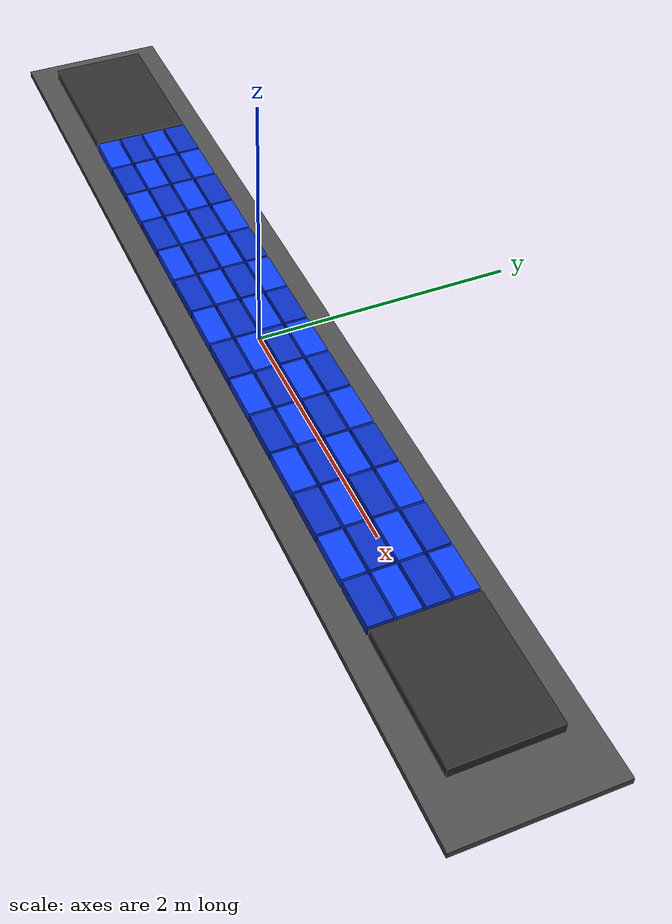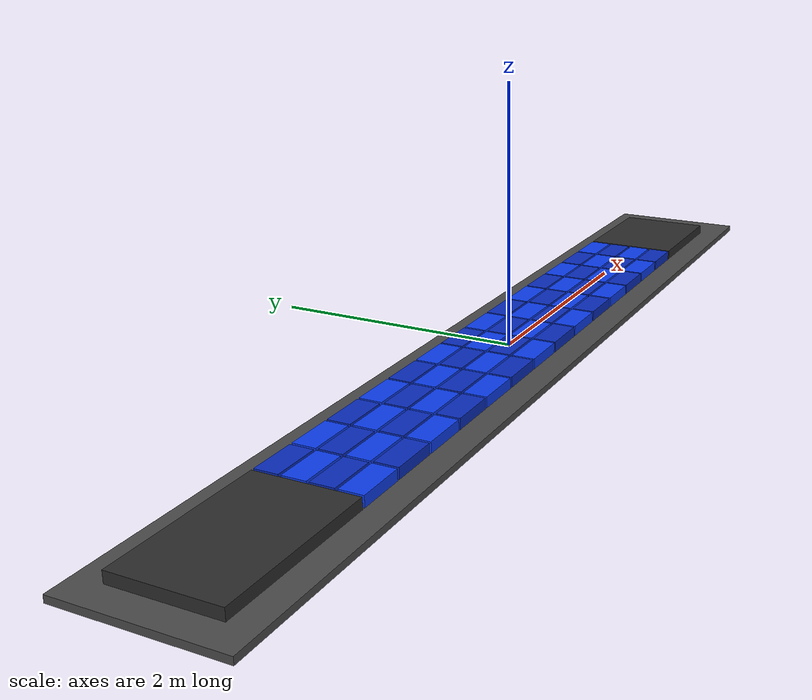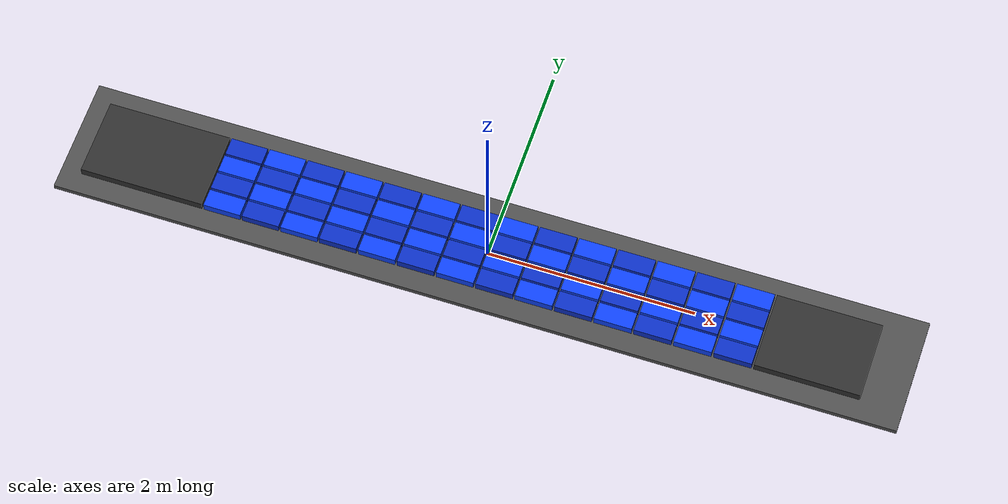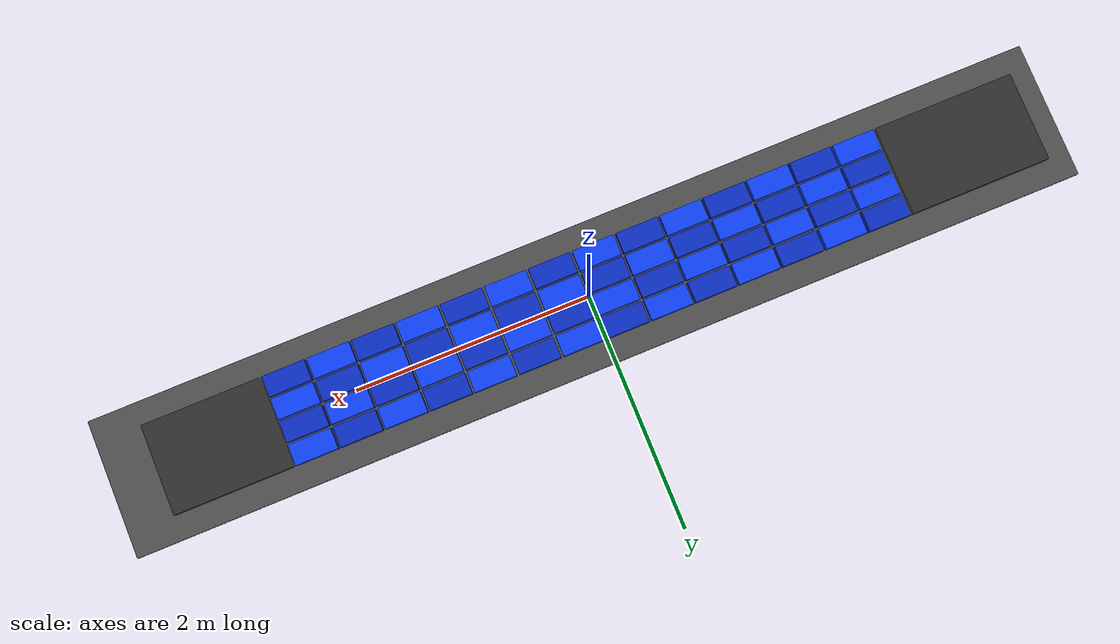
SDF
<?xml version="1.0"?>
<sdf version="1.10">

  <world name="matrix_14x4_stream">

    <gravity>0 0 -9.81</gravity>

    <physics name="physics_1ms" type="ignored">
      <max_step_size>0.001</max_step_size>
      <real_time_factor>1.0</real_time_factor>
      <real_time_update_rate>1000</real_time_update_rate>
    </physics>

    <plugin
      filename="gz-sim-physics-system"
      name="gz::sim::systems::Physics"/>

    <plugin
      filename="gz-sim-user-commands-system"
      name="gz::sim::systems::UserCommands"/>

    <plugin
      filename="gz-sim-scene-broadcaster-system"
      name="gz::sim::systems::SceneBroadcaster"/>

    <plugin
      filename="gz-sim-sensors-system"
      name="gz::sim::systems::Sensors">
      <render_engine>ogre2</render_engine>
    </plugin>

    <light type="directional" name="sun">
      <pose>0 0 6 0 0 0</pose>
      <cast_shadows>false</cast_shadows>

      <diffuse>0.9 0.9 0.9 1</diffuse>
      <specular>0.2 0.2 0.2 1</specular>

      <direction>-0.4 0.2 -1.0</direction>
    </light>

    <!-- Основание находится ниже рабочих поверхностей. -->
    <model name="platform">
      <static>true</static>

      <pose>0 0 -0.025 0 0 0</pose>

      <link name="platform_link">

        <collision name="platform_collision">
          <geometry>
            <box>
              <size>
                8.140000
                1.160000
                0.05
              </size>
            </box>
          </geometry>
        </collision>

        <visual name="platform_visual">
          <geometry>
            <box>
              <size>
                8.140000
                1.160000
                0.05
              </size>
            </box>
          </geometry>

          <material>
            <ambient>0.20 0.20 0.20 1</ambient>
            <diffuse>0.30 0.30 0.30 1</diffuse>
          </material>
        </visual>

      </link>
    </model>

    <model name="infeed_conveyor">
      <static>true</static>

      <pose>-3.270000 0.000000 0 0 0 0</pose>

      <link name="belt">
        <pose>0 0 0.040000 0 0 0</pose>

        <collision name="belt_collision">
	<max_contacts>4</max_contacts>
          <geometry>
            <box>
              <size>1.200000 0.760000 0.080000</size>
            </box>
          </geometry>

          <surface>
            <friction>
              <ode>
                <!-- Продольное сцепление вдоль X -->
                <mu>0.8</mu>

                <!-- Поперечное сцепление вдоль Y -->
                <mu2>0.2</mu2>

                <fdir1>1 0 0</fdir1>
              </ode>
            </friction>
          </surface>
        </collision>

        <visual name="belt_visual">
          <geometry>
            <box>
              <size>1.200000 0.760000 0.080000</size>
            </box>
          </geometry>

          <material>
            <ambient>0.180 0.180 0.180 1</ambient>
            <diffuse>0.180 0.180 0.180 1</diffuse>
          </material>
        </visual>

      </link>

      <plugin
        filename="gz-sim-track-controller-system"
        name="gz::sim::systems::TrackController">

        <link>belt</link>

        <!-- Положительное направление скорости: глобальная ось +X -->
        <track_orientation>0 0 0</track_orientation>

        <velocity_topic>/singulator/infeed/cmd_vel</velocity_topic>
        <odometry_topic>/singulator/infeed/odometry</odometry_topic>

        <odometry_publish_frequency>
          1
        </odometry_publish_frequency>

        <min_velocity>-2.0</min_velocity>
        <max_velocity>2.0</max_velocity>

        <min_acceleration>-2.5</min_acceleration>
        <max_acceleration>2.5</max_acceleration>

        <min_jerk>-10.0</min_jerk>
        <max_jerk>10.0</max_jerk>

        <max_command_age>
          2.0
        </max_command_age>

      </plugin>

    </model>

    <model name="cell_r12_c00">
      <static>true</static>

      <pose>2.090000 -0.292500 0 0 0 0</pose>

      <link name="belt">
        <pose>0 0 0.040000 0 0 0</pose>

        <collision name="belt_collision">
	<max_contacts>4</max_contacts>
          <geometry>
            <box>
              <size>0.360000 0.175000 0.080000</size>
            </box>
          </geometry>

          <surface>
            <friction>
              <ode>
                <!-- Продольное сцепление вдоль X -->
                <mu>0.8</mu>

                <!-- Поперечное сцепление вдоль Y -->
                <mu2>0.2</mu2>

                <fdir1>1 0 0</fdir1>
              </ode>
            </friction>
          </surface>
        </collision>

        <visual name="belt_visual">
          <geometry>
            <box>
              <size>0.360000 0.175000 0.080000</size>
            </box>
          </geometry>

          <material>
            <ambient>0.050 0.250 0.950 1</ambient>
            <diffuse>0.050 0.250 0.950 1</diffuse>
          </material>
        </visual>

      </link>

      <plugin
        filename="gz-sim-track-controller-system"
        name="gz::sim::systems::TrackController">

        <link>belt</link>

        <!-- Положительное направление скорости: глобальная ось +X -->
        <track_orientation>0 0 0</track_orientation>

        <velocity_topic>/singulator/cell/r12_c00/cmd_vel</velocity_topic>
        <odometry_topic>/singulator/cell/r12_c00/odometry</odometry_topic>

        <odometry_publish_frequency>
          1
        </odometry_publish_frequency>

        <min_velocity>-2.0</min_velocity>
        <max_velocity>2.0</max_velocity>

        <min_acceleration>-2.5</min_acceleration>
        <max_acceleration>2.5</max_acceleration>

        <min_jerk>-10.0</min_jerk>
        <max_jerk>10.0</max_jerk>

        <max_command_age>
          2.0
        </max_command_age>

      </plugin>

    </model>

    <model name="cell_r12_c01">
      <static>true</static>

      <pose>2.090000 -0.097500 0 0 0 0</pose>

      <link name="belt">
        <pose>0 0 0.040000 0 0 0</pose>

        <collision name="belt_collision">
	<max_contacts>4</max_contacts>
          <geometry>
            <box>
              <size>0.360000 0.175000 0.080000</size>
            </box>
          </geometry>

          <surface>
            <friction>
              <ode>
                <!-- Продольное сцепление вдоль X -->
                <mu>0.8</mu>

                <!-- Поперечное сцепление вдоль Y -->
                <mu2>0.2</mu2>

                <fdir1>1 0 0</fdir1>
              </ode>
            </friction>
          </surface>
        </collision>

        <visual name="belt_visual">
          <geometry>
            <box>
              <size>0.360000 0.175000 0.080000</size>
            </box>
          </geometry>

          <material>
            <ambient>0.040 0.180 0.750 1</ambient>
            <diffuse>0.040 0.180 0.750 1</diffuse>
          </material>
        </visual>

      </link>

      <plugin
        filename="gz-sim-track-controller-system"
        name="gz::sim::systems::TrackController">

        <link>belt</link>

        <!-- Положительное направление скорости: глобальная ось +X -->
        <track_orientation>0 0 0</track_orientation>

        <velocity_topic>/singulator/cell/r12_c01/cmd_vel</velocity_topic>
        <odometry_topic>/singulator/cell/r12_c01/odometry</odometry_topic>

        <odometry_publish_frequency>
          1
        </odometry_publish_frequency>

        <min_velocity>-2.0</min_velocity>
        <max_velocity>2.0</max_velocity>

        <min_acceleration>-2.5</min_acceleration>
        <max_acceleration>2.5</max_acceleration>

        <min_jerk>-10.0</min_jerk>
        <max_jerk>10.0</max_jerk>

        <max_command_age>
          2.0
        </max_command_age>

      </plugin>

    </model>

    <model name="cell_r12_c02">
      <static>true</static>

      <pose>2.090000 0.097500 0 0 0 0</pose>

      <link name="belt">
        <pose>0 0 0.040000 0 0 0</pose>

        <collision name="belt_collision">
	<max_contacts>4</max_contacts>
          <geometry>
            <box>
              <size>0.360000 0.175000 0.080000</size>
            </box>
          </geometry>

          <surface>
            <friction>
              <ode>
                <!-- Продольное сцепление вдоль X -->
                <mu>0.8</mu>

                <!-- Поперечное сцепление вдоль Y -->
                <mu2>0.2</mu2>

                <fdir1>1 0 0</fdir1>
              </ode>
            </friction>
          </surface>
        </collision>

        <visual name="belt_visual">
          <geometry>
            <box>
              <size>0.360000 0.175000 0.080000</size>
            </box>
          </geometry>

          <material>
            <ambient>0.050 0.250 0.950 1</ambient>
            <diffuse>0.050 0.250 0.950 1</diffuse>
          </material>
        </visual>

      </link>

      <plugin
        filename="gz-sim-track-controller-system"
        name="gz::sim::systems::TrackController">

        <link>belt</link>

        <!-- Положительное направление скорости: глобальная ось +X -->
        <track_orientation>0 0 0</track_orientation>

        <velocity_topic>/singulator/cell/r12_c02/cmd_vel</velocity_topic>
        <odometry_topic>/singulator/cell/r12_c02/odometry</odometry_topic>

        <odometry_publish_frequency>
          1
        </odometry_publish_frequency>

        <min_velocity>-2.0</min_velocity>
        <max_velocity>2.0</max_velocity>

        <min_acceleration>-2.5</min_acceleration>
        <max_acceleration>2.5</max_acceleration>

        <min_jerk>-10.0</min_jerk>
        <max_jerk>10.0</max_jerk>

        <max_command_age>
          2.0
        </max_command_age>

      </plugin>

    </model>

    <model name="cell_r12_c03">
      <static>true</static>

      <pose>2.090000 0.292500 0 0 0 0</pose>

      <link name="belt">
        <pose>0 0 0.040000 0 0 0</pose>

        <collision name="belt_collision">
	<max_contacts>4</max_contacts>
          <geometry>
            <box>
              <size>0.360000 0.175000 0.080000</size>
            </box>
          </geometry>

          <surface>
            <friction>
              <ode>
                <!-- Продольное сцепление вдоль X -->
                <mu>0.8</mu>

                <!-- Поперечное сцепление вдоль Y -->
                <mu2>0.2</mu2>

                <fdir1>1 0 0</fdir1>
              </ode>
            </friction>
          </surface>
        </collision>

        <visual name="belt_visual">
          <geometry>
            <box>
              <size>0.360000 0.175000 0.080000</size>
            </box>
          </geometry>

          <material>
            <ambient>0.040 0.180 0.750 1</ambient>
            <diffuse>0.040 0.180 0.750 1</diffuse>
          </material>
        </visual>

      </link>

      <plugin
        filename="gz-sim-track-controller-system"
        name="gz::sim::systems::TrackController">

        <link>belt</link>

        <!-- Положительное направление скорости: глобальная ось +X -->
        <track_orientation>0 0 0</track_orientation>

        <velocity_topic>/singulator/cell/r12_c03/cmd_vel</velocity_topic>
        <odometry_topic>/singulator/cell/r12_c03/odometry</odometry_topic>

        <odometry_publish_frequency>
          1
        </odometry_publish_frequency>

        <min_velocity>-2.0</min_velocity>
        <max_velocity>2.0</max_velocity>

        <min_acceleration>-2.5</min_acceleration>
        <max_acceleration>2.5</max_acceleration>

        <min_jerk>-10.0</min_jerk>
        <max_jerk>10.0</max_jerk>

        <max_command_age>
          2.0
        </max_command_age>

      </plugin>

    </model>

    <model name="cell_r13_c00">
      <static>true</static>

      <pose>2.470000 -0.292500 0 0 0 0</pose>

      <link name="belt">
        <pose>0 0 0.040000 0 0 0</pose>

        <collision name="belt_collision">
	<max_contacts>4</max_contacts>
          <geometry>
            <box>
              <size>0.360000 0.175000 0.080000</size>
            </box>
          </geometry>

          <surface>
            <friction>
              <ode>
                <!-- Продольное сцепление вдоль X -->
                <mu>0.8</mu>

                <!-- Поперечное сцепление вдоль Y -->
                <mu2>0.2</mu2>

                <fdir1>1 0 0</fdir1>
              </ode>
            </friction>
          </surface>
        </collision>

        <visual name="belt_visual">
          <geometry>
            <box>
              <size>0.360000 0.175000 0.080000</size>
            </box>
          </geometry>

          <material>
            <ambient>0.040 0.180 0.750 1</ambient>
            <diffuse>0.040 0.180 0.750 1</diffuse>
          </material>
        </visual>

      </link>

      <plugin
        filename="gz-sim-track-controller-system"
        name="gz::sim::systems::TrackController">

        <link>belt</link>

        <!-- Положительное направление скорости: глобальная ось +X -->
        <track_orientation>0 0 0</track_orientation>

        <velocity_topic>/singulator/cell/r13_c00/cmd_vel</velocity_topic>
        <odometry_topic>/singulator/cell/r13_c00/odometry</odometry_topic>

        <odometry_publish_frequency>
          1
        </odometry_publish_frequency>

        <min_velocity>-2.0</min_velocity>
        <max_velocity>2.0</max_velocity>

        <min_acceleration>-2.5</min_acceleration>
        <max_acceleration>2.5</max_acceleration>

        <min_jerk>-10.0</min_jerk>
        <max_jerk>10.0</max_jerk>

        <max_command_age>
          2.0
        </max_command_age>

      </plugin>

    </model>

    <model name="cell_r13_c01">
      <static>true</static>

      <pose>2.470000 -0.097500 0 0 0 0</pose>

      <link name="belt">
        <pose>0 0 0.040000 0 0 0</pose>

        <collision name="belt_collision">
	<max_contacts>4</max_contacts>
          <geometry>
            <box>
              <size>0.360000 0.175000 0.080000</size>
            </box>
          </geometry>

          <surface>
            <friction>
              <ode>
                <!-- Продольное сцепление вдоль X -->
                <mu>0.8</mu>

                <!-- Поперечное сцепление вдоль Y -->
                <mu2>0.2</mu2>

                <fdir1>1 0 0</fdir1>
              </ode>
            </friction>
          </surface>
        </collision>

        <visual name="belt_visual">
          <geometry>
            <box>
              <size>0.360000 0.175000 0.080000</size>
            </box>
          </geometry>

          <material>
            <ambient>0.050 0.250 0.950 1</ambient>
            <diffuse>0.050 0.250 0.950 1</diffuse>
          </material>
        </visual>

      </link>

      <plugin
        filename="gz-sim-track-controller-system"
        name="gz::sim::systems::TrackController">

        <link>belt</link>

        <!-- Положительное направление скорости: глобальная ось +X -->
        <track_orientation>0 0 0</track_orientation>

        <velocity_topic>/singulator/cell/r13_c01/cmd_vel</velocity_topic>
        <odometry_topic>/singulator/cell/r13_c01/odometry</odometry_topic>

        <odometry_publish_frequency>
          1
        </odometry_publish_frequency>

        <min_velocity>-2.0</min_velocity>
        <max_velocity>2.0</max_velocity>

        <min_acceleration>-2.5</min_acceleration>
        <max_acceleration>2.5</max_acceleration>

        <min_jerk>-10.0</min_jerk>
        <max_jerk>10.0</max_jerk>

        <max_command_age>
          2.0
        </max_command_age>

      </plugin>

    </model>

    <model name="cell_r13_c02">
      <static>true</static>

      <pose>2.470000 0.097500 0 0 0 0</pose>

      <link name="belt">
        <pose>0 0 0.040000 0 0 0</pose>

        <collision name="belt_collision">
	<max_contacts>4</max_contacts>
          <geometry>
            <box>
              <size>0.360000 0.175000 0.080000</size>
            </box>
          </geometry>

          <surface>
            <friction>
              <ode>
                <!-- Продольное сцепление вдоль X -->
                <mu>0.8</mu>

                <!-- Поперечное сцепление вдоль Y -->
                <mu2>0.2</mu2>

                <fdir1>1 0 0</fdir1>
              </ode>
            </friction>
          </surface>
        </collision>

        <visual name="belt_visual">
          <geometry>
            <box>
              <size>0.360000 0.175000 0.080000</size>
            </box>
          </geometry>

          <material>
            <ambient>0.040 0.180 0.750 1</ambient>
            <diffuse>0.040 0.180 0.750 1</diffuse>
          </material>
        </visual>

      </link>

      <plugin
        filename="gz-sim-track-controller-system"
        name="gz::sim::systems::TrackController">

        <link>belt</link>

        <!-- Положительное направление скорости: глобальная ось +X -->
        <track_orientation>0 0 0</track_orientation>

        <velocity_topic>/singulator/cell/r13_c02/cmd_vel</velocity_topic>
        <odometry_topic>/singulator/cell/r13_c02/odometry</odometry_topic>

        <odometry_publish_frequency>
          1
        </odometry_publish_frequency>

        <min_velocity>-2.0</min_velocity>
        <max_velocity>2.0</max_velocity>

        <min_acceleration>-2.5</min_acceleration>
        <max_acceleration>2.5</max_acceleration>

        <min_jerk>-10.0</min_jerk>
        <max_jerk>10.0</max_jerk>

        <max_command_age>
          2.0
        </max_command_age>

      </plugin>

    </model>

    <model name="cell_r13_c03">
      <static>true</static>

      <pose>2.470000 0.292500 0 0 0 0</pose>

      <link name="belt">
        <pose>0 0 0.040000 0 0 0</pose>

        <collision name="belt_collision">
	<max_contacts>4</max_contacts>
          <geometry>
            <box>
              <size>0.360000 0.175000 0.080000</size>
            </box>
          </geometry>

          <surface>
            <friction>
              <ode>
                <!-- Продольное сцепление вдоль X -->
                <mu>0.8</mu>

                <!-- Поперечное сцепление вдоль Y -->
                <mu2>0.2</mu2>

                <fdir1>1 0 0</fdir1>
              </ode>
            </friction>
          </surface>
        </collision>

        <visual name="belt_visual">
          <geometry>
            <box>
              <size>0.360000 0.175000 0.080000</size>
            </box>
          </geometry>

          <material>
            <ambient>0.050 0.250 0.950 1</ambient>
            <diffuse>0.050 0.250 0.950 1</diffuse>
          </material>
        </visual>

      </link>

      <plugin
        filename="gz-sim-track-controller-system"
        name="gz::sim::systems::TrackController">

        <link>belt</link>

        <!-- Положительное направление скорости: глобальная ось +X -->
        <track_orientation>0 0 0</track_orientation>

        <velocity_topic>/singulator/cell/r13_c03/cmd_vel</velocity_topic>
        <odometry_topic>/singulator/cell/r13_c03/odometry</odometry_topic>

        <odometry_publish_frequency>
          1
        </odometry_publish_frequency>

        <min_velocity>-2.0</min_velocity>
        <max_velocity>2.0</max_velocity>

        <min_acceleration>-2.5</min_acceleration>
        <max_acceleration>2.5</max_acceleration>

        <min_jerk>-10.0</min_jerk>
        <max_jerk>10.0</max_jerk>

        <max_command_age>
          2.0
        </max_command_age>

      </plugin>

    </model>

    <model name="cell_r00_c00">
      <static>true</static>

      <pose>-2.470000 -0.292500 0 0 0 0</pose>

      <link name="belt">
        <pose>0 0 0.040000 0 0 0</pose>

        <collision name="belt_collision">
	<max_contacts>4</max_contacts>
          <geometry>
            <box>
              <size>0.360000 0.175000 0.080000</size>
            </box>
          </geometry>

          <surface>
            <friction>
              <ode>
                <!-- Продольное сцепление вдоль X -->
                <mu>0.8</mu>

                <!-- Поперечное сцепление вдоль Y -->
                <mu2>0.2</mu2>

                <fdir1>1 0 0</fdir1>
              </ode>
            </friction>
          </surface>
        </collision>

        <visual name="belt_visual">
          <geometry>
            <box>
              <size>0.360000 0.175000 0.080000</size>
            </box>
          </geometry>

          <material>
            <ambient>0.050 0.250 0.950 1</ambient>
            <diffuse>0.050 0.250 0.950 1</diffuse>
          </material>
        </visual>

      </link>

      <plugin
        filename="gz-sim-track-controller-system"
        name="gz::sim::systems::TrackController">

        <link>belt</link>

        <!-- Положительное направление скорости: глобальная ось +X -->
        <track_orientation>0 0 0</track_orientation>

        <velocity_topic>/singulator/cell/r00_c00/cmd_vel</velocity_topic>
        <odometry_topic>/singulator/cell/r00_c00/odometry</odometry_topic>

        <odometry_publish_frequency>
          1
        </odometry_publish_frequency>

        <min_velocity>-2.0</min_velocity>
        <max_velocity>2.0</max_velocity>

        <min_acceleration>-2.5</min_acceleration>
        <max_acceleration>2.5</max_acceleration>

        <min_jerk>-10.0</min_jerk>
        <max_jerk>10.0</max_jerk>

        <max_command_age>
          2.0
        </max_command_age>

      </plugin>

    </model>

    <model name="cell_r00_c01">
      <static>true</static>

      <pose>-2.470000 -0.097500 0 0 0 0</pose>

      <link name="belt">
        <pose>0 0 0.040000 0 0 0</pose>

        <collision name="belt_collision">
	<max_contacts>4</max_contacts>
          <geometry>
            <box>
              <size>0.360000 0.175000 0.080000</size>
            </box>
          </geometry>

          <surface>
            <friction>
              <ode>
                <!-- Продольное сцепление вдоль X -->
                <mu>0.8</mu>

                <!-- Поперечное сцепление вдоль Y -->
                <mu2>0.2</mu2>

                <fdir1>1 0 0</fdir1>
              </ode>
            </friction>
          </surface>
        </collision>

        <visual name="belt_visual">
          <geometry>
            <box>
              <size>0.360000 0.175000 0.080000</size>
            </box>
          </geometry>

          <material>
            <ambient>0.040 0.180 0.750 1</ambient>
            <diffuse>0.040 0.180 0.750 1</diffuse>
          </material>
        </visual>

      </link>

      <plugin
        filename="gz-sim-track-controller-system"
        name="gz::sim::systems::TrackController">

        <link>belt</link>

        <!-- Положительное направление скорости: глобальная ось +X -->
        <track_orientation>0 0 0</track_orientation>

        <velocity_topic>/singulator/cell/r00_c01/cmd_vel</velocity_topic>
        <odometry_topic>/singulator/cell/r00_c01/odometry</odometry_topic>

        <odometry_publish_frequency>
          1
        </odometry_publish_frequency>

        <min_velocity>-2.0</min_velocity>
        <max_velocity>2.0</max_velocity>

        <min_acceleration>-2.5</min_acceleration>
        <max_acceleration>2.5</max_acceleration>

        <min_jerk>-10.0</min_jerk>
        <max_jerk>10.0</max_jerk>

        <max_command_age>
          2.0
        </max_command_age>

      </plugin>

    </model>

    <model name="cell_r00_c02">
      <static>true</static>

      <pose>-2.470000 0.097500 0 0 0 0</pose>

      <link name="belt">
        <pose>0 0 0.040000 0 0 0</pose>

        <collision name="belt_collision">
	<max_contacts>4</max_contacts>
          <geometry>
            <box>
              <size>0.360000 0.175000 0.080000</size>
            </box>
          </geometry>

          <surface>
            <friction>
              <ode>
                <!-- Продольное сцепление вдоль X -->
                <mu>0.8</mu>

                <!-- Поперечное сцепление вдоль Y -->
                <mu2>0.2</mu2>

                <fdir1>1 0 0</fdir1>
              </ode>
            </friction>
          </surface>
        </collision>

        <visual name="belt_visual">
          <geometry>
            <box>
              <size>0.360000 0.175000 0.080000</size>
            </box>
          </geometry>

          <material>
            <ambient>0.050 0.250 0.950 1</ambient>
            <diffuse>0.050 0.250 0.950 1</diffuse>
          </material>
        </visual>

      </link>

      <plugin
        filename="gz-sim-track-controller-system"
        name="gz::sim::systems::TrackController">

        <link>belt</link>

        <!-- Положительное направление скорости: глобальная ось +X -->
        <track_orientation>0 0 0</track_orientation>

        <velocity_topic>/singulator/cell/r00_c02/cmd_vel</velocity_topic>
        <odometry_topic>/singulator/cell/r00_c02/odometry</odometry_topic>

        <odometry_publish_frequency>
          1
        </odometry_publish_frequency>

        <min_velocity>-2.0</min_velocity>
        <max_velocity>2.0</max_velocity>

        <min_acceleration>-2.5</min_acceleration>
        <max_acceleration>2.5</max_acceleration>

        <min_jerk>-10.0</min_jerk>
        <max_jerk>10.0</max_jerk>

        <max_command_age>
          2.0
        </max_command_age>

      </plugin>

    </model>

    <model name="cell_r00_c03">
      <static>true</static>

      <pose>-2.470000 0.292500 0 0 0 0</pose>

      <link name="belt">
        <pose>0 0 0.040000 0 0 0</pose>

        <collision name="belt_collision">
	<max_contacts>4</max_contacts>
          <geometry>
            <box>
              <size>0.360000 0.175000 0.080000</size>
            </box>
          </geometry>

          <surface>
            <friction>
              <ode>
                <!-- Продольное сцепление вдоль X -->
                <mu>0.8</mu>

                <!-- Поперечное сцепление вдоль Y -->
                <mu2>0.2</mu2>

                <fdir1>1 0 0</fdir1>
              </ode>
            </friction>
          </surface>
        </collision>

        <visual name="belt_visual">
          <geometry>
            <box>
              <size>0.360000 0.175000 0.080000</size>
            </box>
          </geometry>

          <material>
            <ambient>0.040 0.180 0.750 1</ambient>
            <diffuse>0.040 0.180 0.750 1</diffuse>
          </material>
        </visual>

      </link>

      <plugin
        filename="gz-sim-track-controller-system"
        name="gz::sim::systems::TrackController">

        <link>belt</link>

        <!-- Положительное направление скорости: глобальная ось +X -->
        <track_orientation>0 0 0</track_orientation>

        <velocity_topic>/singulator/cell/r00_c03/cmd_vel</velocity_topic>
        <odometry_topic>/singulator/cell/r00_c03/odometry</odometry_topic>

        <odometry_publish_frequency>
          1
        </odometry_publish_frequency>

        <min_velocity>-2.0</min_velocity>
        <max_velocity>2.0</max_velocity>

        <min_acceleration>-2.5</min_acceleration>
        <max_acceleration>2.5</max_acceleration>

        <min_jerk>-10.0</min_jerk>
        <max_jerk>10.0</max_jerk>

        <max_command_age>
          2.0
        </max_command_age>

      </plugin>

    </model>

    <model name="cell_r01_c00">
      <static>true</static>

      <pose>-2.090000 -0.292500 0 0 0 0</pose>

      <link name="belt">
        <pose>0 0 0.040000 0 0 0</pose>

        <collision name="belt_collision">
	<max_contacts>4</max_contacts>
          <geometry>
            <box>
              <size>0.360000 0.175000 0.080000</size>
            </box>
          </geometry>

          <surface>
            <friction>
              <ode>
                <!-- Продольное сцепление вдоль X -->
                <mu>0.8</mu>

                <!-- Поперечное сцепление вдоль Y -->
                <mu2>0.2</mu2>

                <fdir1>1 0 0</fdir1>
              </ode>
            </friction>
          </surface>
        </collision>

        <visual name="belt_visual">
          <geometry>
            <box>
              <size>0.360000 0.175000 0.080000</size>
            </box>
          </geometry>

          <material>
            <ambient>0.040 0.180 0.750 1</ambient>
            <diffuse>0.040 0.180 0.750 1</diffuse>
          </material>
        </visual>

      </link>

      <plugin
        filename="gz-sim-track-controller-system"
        name="gz::sim::systems::TrackController">

        <link>belt</link>

        <!-- Положительное направление скорости: глобальная ось +X -->
        <track_orientation>0 0 0</track_orientation>

        <velocity_topic>/singulator/cell/r01_c00/cmd_vel</velocity_topic>
        <odometry_topic>/singulator/cell/r01_c00/odometry</odometry_topic>

        <odometry_publish_frequency>
          1
        </odometry_publish_frequency>

        <min_velocity>-2.0</min_velocity>
        <max_velocity>2.0</max_velocity>

        <min_acceleration>-2.5</min_acceleration>
        <max_acceleration>2.5</max_acceleration>

        <min_jerk>-10.0</min_jerk>
        <max_jerk>10.0</max_jerk>

        <max_command_age>
          2.0
        </max_command_age>

      </plugin>

    </model>

    <model name="cell_r01_c01">
      <static>true</static>

      <pose>-2.090000 -0.097500 0 0 0 0</pose>

      <link name="belt">
        <pose>0 0 0.040000 0 0 0</pose>

        <collision name="belt_collision">
	<max_contacts>4</max_contacts>
          <geometry>
            <box>
              <size>0.360000 0.175000 0.080000</size>
            </box>
          </geometry>

          <surface>
            <friction>
              <ode>
                <!-- Продольное сцепление вдоль X -->
                <mu>0.8</mu>

                <!-- Поперечное сцепление вдоль Y -->
                <mu2>0.2</mu2>

                <fdir1>1 0 0</fdir1>
              </ode>
            </friction>
          </surface>
        </collision>

        <visual name="belt_visual">
          <geometry>
            <box>
              <size>0.360000 0.175000 0.080000</size>
            </box>
          </geometry>

          <material>
            <ambient>0.050 0.250 0.950 1</ambient>
            <diffuse>0.050 0.250 0.950 1</diffuse>
          </material>
        </visual>

      </link>

      <plugin
        filename="gz-sim-track-controller-system"
        name="gz::sim::systems::TrackController">

        <link>belt</link>

        <!-- Положительное направление скорости: глобальная ось +X -->
        <track_orientation>0 0 0</track_orientation>

        <velocity_topic>/singulator/cell/r01_c01/cmd_vel</velocity_topic>
        <odometry_topic>/singulator/cell/r01_c01/odometry</odometry_topic>

        <odometry_publish_frequency>
          1
        </odometry_publish_frequency>

        <min_velocity>-2.0</min_velocity>
        <max_velocity>2.0</max_velocity>

        <min_acceleration>-2.5</min_acceleration>
        <max_acceleration>2.5</max_acceleration>

        <min_jerk>-10.0</min_jerk>
        <max_jerk>10.0</max_jerk>

        <max_command_age>
          2.0
        </max_command_age>

      </plugin>

    </model>

    <model name="cell_r01_c02">
      <static>true</static>

      <pose>-2.090000 0.097500 0 0 0 0</pose>

      <link name="belt">
        <pose>0 0 0.040000 0 0 0</pose>

        <collision name="belt_collision">
	<max_contacts>4</max_contacts>
          <geometry>
            <box>
              <size>0.360000 0.175000 0.080000</size>
            </box>
          </geometry>

          <surface>
            <friction>
              <ode>
                <!-- Продольное сцепление вдоль X -->
                <mu>0.8</mu>

                <!-- Поперечное сцепление вдоль Y -->
                <mu2>0.2</mu2>

                <fdir1>1 0 0</fdir1>
              </ode>
            </friction>
          </surface>
        </collision>

        <visual name="belt_visual">
          <geometry>
            <box>
              <size>0.360000 0.175000 0.080000</size>
            </box>
          </geometry>

          <material>
            <ambient>0.040 0.180 0.750 1</ambient>
            <diffuse>0.040 0.180 0.750 1</diffuse>
          </material>
        </visual>

      </link>

      <plugin
        filename="gz-sim-track-controller-system"
        name="gz::sim::systems::TrackController">

        <link>belt</link>

        <!-- Положительное направление скорости: глобальная ось +X -->
        <track_orientation>0 0 0</track_orientation>

        <velocity_topic>/singulator/cell/r01_c02/cmd_vel</velocity_topic>
        <odometry_topic>/singulator/cell/r01_c02/odometry</odometry_topic>

        <odometry_publish_frequency>
          1
        </odometry_publish_frequency>

        <min_velocity>-2.0</min_velocity>
        <max_velocity>2.0</max_velocity>

        <min_acceleration>-2.5</min_acceleration>
        <max_acceleration>2.5</max_acceleration>

        <min_jerk>-10.0</min_jerk>
        <max_jerk>10.0</max_jerk>

        <max_command_age>
          2.0
        </max_command_age>

      </plugin>

    </model>

    <model name="cell_r01_c03">
      <static>true</static>

      <pose>-2.090000 0.292500 0 0 0 0</pose>

      <link name="belt">
        <pose>0 0 0.040000 0 0 0</pose>

        <collision name="belt_collision">
	<max_contacts>4</max_contacts>
          <geometry>
            <box>
              <size>0.360000 0.175000 0.080000</size>
            </box>
          </geometry>

          <surface>
            <friction>
              <ode>
                <!-- Продольное сцепление вдоль X -->
                <mu>0.8</mu>

                <!-- Поперечное сцепление вдоль Y -->
                <mu2>0.2</mu2>

                <fdir1>1 0 0</fdir1>
              </ode>
            </friction>
          </surface>
        </collision>

        <visual name="belt_visual">
          <geometry>
            <box>
              <size>0.360000 0.175000 0.080000</size>
            </box>
          </geometry>

          <material>
            <ambient>0.050 0.250 0.950 1</ambient>
            <diffuse>0.050 0.250 0.950 1</diffuse>
          </material>
        </visual>

      </link>

      <plugin
        filename="gz-sim-track-controller-system"
        name="gz::sim::systems::TrackController">

        <link>belt</link>

        <!-- Положительное направление скорости: глобальная ось +X -->
        <track_orientation>0 0 0</track_orientation>

        <velocity_topic>/singulator/cell/r01_c03/cmd_vel</velocity_topic>
        <odometry_topic>/singulator/cell/r01_c03/odometry</odometry_topic>

        <odometry_publish_frequency>
          1
        </odometry_publish_frequency>

        <min_velocity>-2.0</min_velocity>
        <max_velocity>2.0</max_velocity>

        <min_acceleration>-2.5</min_acceleration>
        <max_acceleration>2.5</max_acceleration>

        <min_jerk>-10.0</min_jerk>
        <max_jerk>10.0</max_jerk>

        <max_command_age>
          2.0
        </max_command_age>

      </plugin>

    </model>

    <model name="cell_r02_c00">
      <static>true</static>

      <pose>-1.710000 -0.292500 0 0 0 0</pose>

      <link name="belt">
        <pose>0 0 0.040000 0 0 0</pose>

        <collision name="belt_collision">
	<max_contacts>4</max_contacts>
          <geometry>
            <box>
              <size>0.360000 0.175000 0.080000</size>
            </box>
          </geometry>

          <surface>
            <friction>
              <ode>
                <!-- Продольное сцепление вдоль X -->
                <mu>0.8</mu>

                <!-- Поперечное сцепление вдоль Y -->
                <mu2>0.2</mu2>

                <fdir1>1 0 0</fdir1>
              </ode>
            </friction>
          </surface>
        </collision>

        <visual name="belt_visual">
          <geometry>
            <box>
              <size>0.360000 0.175000 0.080000</size>
            </box>
          </geometry>

          <material>
            <ambient>0.050 0.250 0.950 1</ambient>
            <diffuse>0.050 0.250 0.950 1</diffuse>
          </material>
        </visual>

      </link>

      <plugin
        filename="gz-sim-track-controller-system"
        name="gz::sim::systems::TrackController">

        <link>belt</link>

        <!-- Положительное направление скорости: глобальная ось +X -->
        <track_orientation>0 0 0</track_orientation>

        <velocity_topic>/singulator/cell/r02_c00/cmd_vel</velocity_topic>
        <odometry_topic>/singulator/cell/r02_c00/odometry</odometry_topic>

        <odometry_publish_frequency>
          1
        </odometry_publish_frequency>

        <min_velocity>-2.0</min_velocity>
        <max_velocity>2.0</max_velocity>

        <min_acceleration>-2.5</min_acceleration>
        <max_acceleration>2.5</max_acceleration>

        <min_jerk>-10.0</min_jerk>
        <max_jerk>10.0</max_jerk>

        <max_command_age>
          2.0
        </max_command_age>

      </plugin>

    </model>

    <model name="cell_r02_c01">
      <static>true</static>

      <pose>-1.710000 -0.097500 0 0 0 0</pose>

      <link name="belt">
        <pose>0 0 0.040000 0 0 0</pose>

        <collision name="belt_collision">
	<max_contacts>4</max_contacts>
          <geometry>
            <box>
              <size>0.360000 0.175000 0.080000</size>
            </box>
          </geometry>

          <surface>
            <friction>
              <ode>
                <!-- Продольное сцепление вдоль X -->
                <mu>0.8</mu>

                <!-- Поперечное сцепление вдоль Y -->
                <mu2>0.2</mu2>

                <fdir1>1 0 0</fdir1>
              </ode>
            </friction>
          </surface>
        </collision>

        <visual name="belt_visual">
          <geometry>
            <box>
              <size>0.360000 0.175000 0.080000</size>
            </box>
          </geometry>

          <material>
            <ambient>0.040 0.180 0.750 1</ambient>
            <diffuse>0.040 0.180 0.750 1</diffuse>
          </material>
        </visual>

      </link>

      <plugin
        filename="gz-sim-track-controller-system"
        name="gz::sim::systems::TrackController">

        <link>belt</link>

        <!-- Положительное направление скорости: глобальная ось +X -->
        <track_orientation>0 0 0</track_orientation>

        <velocity_topic>/singulator/cell/r02_c01/cmd_vel</velocity_topic>
        <odometry_topic>/singulator/cell/r02_c01/odometry</odometry_topic>

        <odometry_publish_frequency>
          1
        </odometry_publish_frequency>

        <min_velocity>-2.0</min_velocity>
        <max_velocity>2.0</max_velocity>

        <min_acceleration>-2.5</min_acceleration>
        <max_acceleration>2.5</max_acceleration>

        <min_jerk>-10.0</min_jerk>
        <max_jerk>10.0</max_jerk>

        <max_command_age>
          2.0
        </max_command_age>

      </plugin>

    </model>

    <model name="cell_r02_c02">
      <static>true</static>

      <pose>-1.710000 0.097500 0 0 0 0</pose>

      <link name="belt">
        <pose>0 0 0.040000 0 0 0</pose>

        <collision name="belt_collision">
	<max_contacts>4</max_contacts>
          <geometry>
            <box>
              <size>0.360000 0.175000 0.080000</size>
            </box>
          </geometry>

          <surface>
            <friction>
              <ode>
                <!-- Продольное сцепление вдоль X -->
                <mu>0.8</mu>

                <!-- Поперечное сцепление вдоль Y -->
                <mu2>0.2</mu2>

                <fdir1>1 0 0</fdir1>
              </ode>
            </friction>
          </surface>
        </collision>

        <visual name="belt_visual">
          <geometry>
            <box>
              <size>0.360000 0.175000 0.080000</size>
            </box>
          </geometry>

          <material>
            <ambient>0.050 0.250 0.950 1</ambient>
            <diffuse>0.050 0.250 0.950 1</diffuse>
          </material>
        </visual>

      </link>

      <plugin
        filename="gz-sim-track-controller-system"
        name="gz::sim::systems::TrackController">

        <link>belt</link>

        <!-- Положительное направление скорости: глобальная ось +X -->
        <track_orientation>0 0 0</track_orientation>

        <velocity_topic>/singulator/cell/r02_c02/cmd_vel</velocity_topic>
        <odometry_topic>/singulator/cell/r02_c02/odometry</odometry_topic>

        <odometry_publish_frequency>
          1
        </odometry_publish_frequency>

        <min_velocity>-2.0</min_velocity>
        <max_velocity>2.0</max_velocity>

        <min_acceleration>-2.5</min_acceleration>
        <max_acceleration>2.5</max_acceleration>

        <min_jerk>-10.0</min_jerk>
        <max_jerk>10.0</max_jerk>

        <max_command_age>
          2.0
        </max_command_age>

      </plugin>

    </model>

    <model name="cell_r02_c03">
      <static>true</static>

      <pose>-1.710000 0.292500 0 0 0 0</pose>

      <link name="belt">
        <pose>0 0 0.040000 0 0 0</pose>

        <collision name="belt_collision">
	<max_contacts>4</max_contacts>
          <geometry>
            <box>
              <size>0.360000 0.175000 0.080000</size>
            </box>
          </geometry>

          <surface>
            <friction>
              <ode>
                <!-- Продольное сцепление вдоль X -->
                <mu>0.8</mu>

                <!-- Поперечное сцепление вдоль Y -->
                <mu2>0.2</mu2>

                <fdir1>1 0 0</fdir1>
              </ode>
            </friction>
          </surface>
        </collision>

        <visual name="belt_visual">
          <geometry>
            <box>
              <size>0.360000 0.175000 0.080000</size>
            </box>
          </geometry>

          <material>
            <ambient>0.040 0.180 0.750 1</ambient>
            <diffuse>0.040 0.180 0.750 1</diffuse>
          </material>
        </visual>

      </link>

      <plugin
        filename="gz-sim-track-controller-system"
        name="gz::sim::systems::TrackController">

        <link>belt</link>

        <!-- Положительное направление скорости: глобальная ось +X -->
        <track_orientation>0 0 0</track_orientation>

        <velocity_topic>/singulator/cell/r02_c03/cmd_vel</velocity_topic>
        <odometry_topic>/singulator/cell/r02_c03/odometry</odometry_topic>

        <odometry_publish_frequency>
          1
        </odometry_publish_frequency>

        <min_velocity>-2.0</min_velocity>
        <max_velocity>2.0</max_velocity>

        <min_acceleration>-2.5</min_acceleration>
        <max_acceleration>2.5</max_acceleration>

        <min_jerk>-10.0</min_jerk>
        <max_jerk>10.0</max_jerk>

        <max_command_age>
          2.0
        </max_command_age>

      </plugin>

    </model>

    <model name="cell_r03_c00">
      <static>true</static>

      <pose>-1.330000 -0.292500 0 0 0 0</pose>

      <link name="belt">
        <pose>0 0 0.040000 0 0 0</pose>

        <collision name="belt_collision">
	<max_contacts>4</max_contacts>
          <geometry>
            <box>
              <size>0.360000 0.175000 0.080000</size>
            </box>
          </geometry>

          <surface>
            <friction>
              <ode>
                <!-- Продольное сцепление вдоль X -->
                <mu>0.8</mu>

                <!-- Поперечное сцепление вдоль Y -->
                <mu2>0.2</mu2>

                <fdir1>1 0 0</fdir1>
              </ode>
            </friction>
          </surface>
        </collision>

        <visual name="belt_visual">
          <geometry>
            <box>
              <size>0.360000 0.175000 0.080000</size>
            </box>
          </geometry>

          <material>
            <ambient>0.040 0.180 0.750 1</ambient>
            <diffuse>0.040 0.180 0.750 1</diffuse>
          </material>
        </visual>

      </link>

      <plugin
        filename="gz-sim-track-controller-system"
        name="gz::sim::systems::TrackController">

        <link>belt</link>

        <!-- Положительное направление скорости: глобальная ось +X -->
        <track_orientation>0 0 0</track_orientation>

        <velocity_topic>/singulator/cell/r03_c00/cmd_vel</velocity_topic>
        <odometry_topic>/singulator/cell/r03_c00/odometry</odometry_topic>

        <odometry_publish_frequency>
          1
        </odometry_publish_frequency>

        <min_velocity>-2.0</min_velocity>
        <max_velocity>2.0</max_velocity>

        <min_acceleration>-2.5</min_acceleration>
        <max_acceleration>2.5</max_acceleration>

        <min_jerk>-10.0</min_jerk>
        <max_jerk>10.0</max_jerk>

        <max_command_age>
          2.0
        </max_command_age>

      </plugin>

    </model>

    <model name="cell_r03_c01">
      <static>true</static>

      <pose>-1.330000 -0.097500 0 0 0 0</pose>

      <link name="belt">
        <pose>0 0 0.040000 0 0 0</pose>

        <collision name="belt_collision">
	<max_contacts>4</max_contacts>
          <geometry>
            <box>
              <size>0.360000 0.175000 0.080000</size>
            </box>
          </geometry>

          <surface>
            <friction>
              <ode>
                <!-- Продольное сцепление вдоль X -->
                <mu>0.8</mu>

                <!-- Поперечное сцепление вдоль Y -->
                <mu2>0.2</mu2>

                <fdir1>1 0 0</fdir1>
              </ode>
            </friction>
          </surface>
        </collision>

        <visual name="belt_visual">
          <geometry>
            <box>
              <size>0.360000 0.175000 0.080000</size>
            </box>
          </geometry>

          <material>
            <ambient>0.050 0.250 0.950 1</ambient>
            <diffuse>0.050 0.250 0.950 1</diffuse>
          </material>
        </visual>

      </link>

      <plugin
        filename="gz-sim-track-controller-system"
        name="gz::sim::systems::TrackController">

        <link>belt</link>

        <!-- Положительное направление скорости: глобальная ось +X -->
        <track_orientation>0 0 0</track_orientation>

        <velocity_topic>/singulator/cell/r03_c01/cmd_vel</velocity_topic>
        <odometry_topic>/singulator/cell/r03_c01/odometry</odometry_topic>

        <odometry_publish_frequency>
          1
        </odometry_publish_frequency>

        <min_velocity>-2.0</min_velocity>
        <max_velocity>2.0</max_velocity>

        <min_acceleration>-2.5</min_acceleration>
        <max_acceleration>2.5</max_acceleration>

        <min_jerk>-10.0</min_jerk>
        <max_jerk>10.0</max_jerk>

        <max_command_age>
          2.0
        </max_command_age>

      </plugin>

    </model>

    <model name="cell_r03_c02">
      <static>true</static>

      <pose>-1.330000 0.097500 0 0 0 0</pose>

      <link name="belt">
        <pose>0 0 0.040000 0 0 0</pose>

        <collision name="belt_collision">
	<max_contacts>4</max_contacts>
          <geometry>
            <box>
              <size>0.360000 0.175000 0.080000</size>
            </box>
          </geometry>

          <surface>
            <friction>
              <ode>
                <!-- Продольное сцепление вдоль X -->
                <mu>0.8</mu>

                <!-- Поперечное сцепление вдоль Y -->
                <mu2>0.2</mu2>

                <fdir1>1 0 0</fdir1>
              </ode>
            </friction>
          </surface>
        </collision>

        <visual name="belt_visual">
          <geometry>
            <box>
              <size>0.360000 0.175000 0.080000</size>
            </box>
          </geometry>

          <material>
            <ambient>0.040 0.180 0.750 1</ambient>
            <diffuse>0.040 0.180 0.750 1</diffuse>
          </material>
        </visual>

      </link>

      <plugin
        filename="gz-sim-track-controller-system"
        name="gz::sim::systems::TrackController">

        <link>belt</link>

        <!-- Положительное направление скорости: глобальная ось +X -->
        <track_orientation>0 0 0</track_orientation>

        <velocity_topic>/singulator/cell/r03_c02/cmd_vel</velocity_topic>
        <odometry_topic>/singulator/cell/r03_c02/odometry</odometry_topic>

        <odometry_publish_frequency>
          1
        </odometry_publish_frequency>

        <min_velocity>-2.0</min_velocity>
        <max_velocity>2.0</max_velocity>

        <min_acceleration>-2.5</min_acceleration>
        <max_acceleration>2.5</max_acceleration>

        <min_jerk>-10.0</min_jerk>
        <max_jerk>10.0</max_jerk>

        <max_command_age>
          2.0
        </max_command_age>

      </plugin>

    </model>

    <model name="cell_r03_c03">
      <static>true</static>

      <pose>-1.330000 0.292500 0 0 0 0</pose>

      <link name="belt">
        <pose>0 0 0.040000 0 0 0</pose>

        <collision name="belt_collision">
	<max_contacts>4</max_contacts>
          <geometry>
            <box>
              <size>0.360000 0.175000 0.080000</size>
            </box>
          </geometry>

          <surface>
            <friction>
              <ode>
                <!-- Продольное сцепление вдоль X -->
                <mu>0.8</mu>

                <!-- Поперечное сцепление вдоль Y -->
                <mu2>0.2</mu2>

                <fdir1>1 0 0</fdir1>
              </ode>
            </friction>
          </surface>
        </collision>

        <visual name="belt_visual">
          <geometry>
            <box>
              <size>0.360000 0.175000 0.080000</size>
            </box>
          </geometry>

          <material>
            <ambient>0.050 0.250 0.950 1</ambient>
            <diffuse>0.050 0.250 0.950 1</diffuse>
          </material>
        </visual>

      </link>

      <plugin
        filename="gz-sim-track-controller-system"
        name="gz::sim::systems::TrackController">

        <link>belt</link>

        <!-- Положительное направление скорости: глобальная ось +X -->
        <track_orientation>0 0 0</track_orientation>

        <velocity_topic>/singulator/cell/r03_c03/cmd_vel</velocity_topic>
        <odometry_topic>/singulator/cell/r03_c03/odometry</odometry_topic>

        <odometry_publish_frequency>
          1
        </odometry_publish_frequency>

        <min_velocity>-2.0</min_velocity>
        <max_velocity>2.0</max_velocity>

        <min_acceleration>-2.5</min_acceleration>
        <max_acceleration>2.5</max_acceleration>

        <min_jerk>-10.0</min_jerk>
        <max_jerk>10.0</max_jerk>

        <max_command_age>
          2.0
        </max_command_age>

      </plugin>

    </model>

    <model name="cell_r04_c00">
      <static>true</static>

      <pose>-0.950000 -0.292500 0 0 0 0</pose>

      <link name="belt">
        <pose>0 0 0.040000 0 0 0</pose>

        <collision name="belt_collision">
	<max_contacts>4</max_contacts>
          <geometry>
            <box>
              <size>0.360000 0.175000 0.080000</size>
            </box>
          </geometry>

          <surface>
            <friction>
              <ode>
                <!-- Продольное сцепление вдоль X -->
                <mu>0.8</mu>

                <!-- Поперечное сцепление вдоль Y -->
                <mu2>0.2</mu2>

                <fdir1>1 0 0</fdir1>
              </ode>
            </friction>
          </surface>
        </collision>

        <visual name="belt_visual">
          <geometry>
            <box>
              <size>0.360000 0.175000 0.080000</size>
            </box>
          </geometry>

          <material>
            <ambient>0.050 0.250 0.950 1</ambient>
            <diffuse>0.050 0.250 0.950 1</diffuse>
          </material>
        </visual>

      </link>

      <plugin
        filename="gz-sim-track-controller-system"
        name="gz::sim::systems::TrackController">

        <link>belt</link>

        <!-- Положительное направление скорости: глобальная ось +X -->
        <track_orientation>0 0 0</track_orientation>

        <velocity_topic>/singulator/cell/r04_c00/cmd_vel</velocity_topic>
        <odometry_topic>/singulator/cell/r04_c00/odometry</odometry_topic>

        <odometry_publish_frequency>
          1
        </odometry_publish_frequency>

        <min_velocity>-2.0</min_velocity>
        <max_velocity>2.0</max_velocity>

        <min_acceleration>-2.5</min_acceleration>
        <max_acceleration>2.5</max_acceleration>

        <min_jerk>-10.0</min_jerk>
        <max_jerk>10.0</max_jerk>

        <max_command_age>
          2.0
        </max_command_age>

      </plugin>

    </model>

    <model name="cell_r04_c01">
      <static>true</static>

      <pose>-0.950000 -0.097500 0 0 0 0</pose>

      <link name="belt">
        <pose>0 0 0.040000 0 0 0</pose>

        <collision name="belt_collision">
	<max_contacts>4</max_contacts>
          <geometry>
            <box>
              <size>0.360000 0.175000 0.080000</size>
            </box>
          </geometry>

          <surface>
            <friction>
              <ode>
                <!-- Продольное сцепление вдоль X -->
                <mu>0.8</mu>

                <!-- Поперечное сцепление вдоль Y -->
                <mu2>0.2</mu2>

                <fdir1>1 0 0</fdir1>
              </ode>
            </friction>
          </surface>
        </collision>

        <visual name="belt_visual">
          <geometry>
            <box>
              <size>0.360000 0.175000 0.080000</size>
            </box>
          </geometry>

          <material>
            <ambient>0.040 0.180 0.750 1</ambient>
            <diffuse>0.040 0.180 0.750 1</diffuse>
          </material>
        </visual>

      </link>

      <plugin
        filename="gz-sim-track-controller-system"
        name="gz::sim::systems::TrackController">

        <link>belt</link>

        <!-- Положительное направление скорости: глобальная ось +X -->
        <track_orientation>0 0 0</track_orientation>

        <velocity_topic>/singulator/cell/r04_c01/cmd_vel</velocity_topic>
        <odometry_topic>/singulator/cell/r04_c01/odometry</odometry_topic>

        <odometry_publish_frequency>
          1
        </odometry_publish_frequency>

        <min_velocity>-2.0</min_velocity>
        <max_velocity>2.0</max_velocity>

        <min_acceleration>-2.5</min_acceleration>
        <max_acceleration>2.5</max_acceleration>

        <min_jerk>-10.0</min_jerk>
        <max_jerk>10.0</max_jerk>

        <max_command_age>
          2.0
        </max_command_age>

      </plugin>

    </model>

    <model name="cell_r04_c02">
      <static>true</static>

      <pose>-0.950000 0.097500 0 0 0 0</pose>

      <link name="belt">
        <pose>0 0 0.040000 0 0 0</pose>

        <collision name="belt_collision">
	<max_contacts>4</max_contacts>
          <geometry>
            <box>
              <size>0.360000 0.175000 0.080000</size>
            </box>
          </geometry>

          <surface>
            <friction>
              <ode>
                <!-- Продольное сцепление вдоль X -->
                <mu>0.8</mu>

                <!-- Поперечное сцепление вдоль Y -->
                <mu2>0.2</mu2>

                <fdir1>1 0 0</fdir1>
              </ode>
            </friction>
          </surface>
        </collision>

        <visual name="belt_visual">
          <geometry>
            <box>
              <size>0.360000 0.175000 0.080000</size>
            </box>
          </geometry>

          <material>
            <ambient>0.050 0.250 0.950 1</ambient>
            <diffuse>0.050 0.250 0.950 1</diffuse>
          </material>
        </visual>

      </link>

      <plugin
        filename="gz-sim-track-controller-system"
        name="gz::sim::systems::TrackController">

        <link>belt</link>

        <!-- Положительное направление скорости: глобальная ось +X -->
        <track_orientation>0 0 0</track_orientation>

        <velocity_topic>/singulator/cell/r04_c02/cmd_vel</velocity_topic>
        <odometry_topic>/singulator/cell/r04_c02/odometry</odometry_topic>

        <odometry_publish_frequency>
          1
        </odometry_publish_frequency>

        <min_velocity>-2.0</min_velocity>
        <max_velocity>2.0</max_velocity>

        <min_acceleration>-2.5</min_acceleration>
        <max_acceleration>2.5</max_acceleration>

        <min_jerk>-10.0</min_jerk>
        <max_jerk>10.0</max_jerk>

        <max_command_age>
          2.0
        </max_command_age>

      </plugin>

    </model>

    <model name="cell_r04_c03">
      <static>true</static>

      <pose>-0.950000 0.292500 0 0 0 0</pose>

      <link name="belt">
        <pose>0 0 0.040000 0 0 0</pose>

        <collision name="belt_collision">
	<max_contacts>4</max_contacts>
          <geometry>
            <box>
              <size>0.360000 0.175000 0.080000</size>
            </box>
          </geometry>

          <surface>
            <friction>
              <ode>
                <!-- Продольное сцепление вдоль X -->
                <mu>0.8</mu>

                <!-- Поперечное сцепление вдоль Y -->
                <mu2>0.2</mu2>

                <fdir1>1 0 0</fdir1>
              </ode>
            </friction>
          </surface>
        </collision>

        <visual name="belt_visual">
          <geometry>
            <box>
              <size>0.360000 0.175000 0.080000</size>
            </box>
          </geometry>

          <material>
            <ambient>0.040 0.180 0.750 1</ambient>
            <diffuse>0.040 0.180 0.750 1</diffuse>
          </material>
        </visual>

      </link>

      <plugin
        filename="gz-sim-track-controller-system"
        name="gz::sim::systems::TrackController">

        <link>belt</link>

        <!-- Положительное направление скорости: глобальная ось +X -->
        <track_orientation>0 0 0</track_orientation>

        <velocity_topic>/singulator/cell/r04_c03/cmd_vel</velocity_topic>
        <odometry_topic>/singulator/cell/r04_c03/odometry</odometry_topic>

        <odometry_publish_frequency>
          1
        </odometry_publish_frequency>

        <min_velocity>-2.0</min_velocity>
        <max_velocity>2.0</max_velocity>

        <min_acceleration>-2.5</min_acceleration>
        <max_acceleration>2.5</max_acceleration>

        <min_jerk>-10.0</min_jerk>
        <max_jerk>10.0</max_jerk>

        <max_command_age>
          2.0
        </max_command_age>

      </plugin>

    </model>

    <model name="cell_r05_c00">
      <static>true</static>

      <pose>-0.570000 -0.292500 0 0 0 0</pose>

      <link name="belt">
        <pose>0 0 0.040000 0 0 0</pose>

        <collision name="belt_collision">
	<max_contacts>4</max_contacts>
          <geometry>
            <box>
              <size>0.360000 0.175000 0.080000</size>
            </box>
          </geometry>

          <surface>
            <friction>
              <ode>
                <!-- Продольное сцепление вдоль X -->
                <mu>0.8</mu>

                <!-- Поперечное сцепление вдоль Y -->
                <mu2>0.2</mu2>

                <fdir1>1 0 0</fdir1>
              </ode>
            </friction>
          </surface>
        </collision>

        <visual name="belt_visual">
          <geometry>
            <box>
              <size>0.360000 0.175000 0.080000</size>
            </box>
          </geometry>

          <material>
            <ambient>0.040 0.180 0.750 1</ambient>
            <diffuse>0.040 0.180 0.750 1</diffuse>
          </material>
        </visual>

      </link>

      <plugin
        filename="gz-sim-track-controller-system"
        name="gz::sim::systems::TrackController">

        <link>belt</link>

        <!-- Положительное направление скорости: глобальная ось +X -->
        <track_orientation>0 0 0</track_orientation>

        <velocity_topic>/singulator/cell/r05_c00/cmd_vel</velocity_topic>
        <odometry_topic>/singulator/cell/r05_c00/odometry</odometry_topic>

        <odometry_publish_frequency>
          1
        </odometry_publish_frequency>

        <min_velocity>-2.0</min_velocity>
        <max_velocity>2.0</max_velocity>

        <min_acceleration>-2.5</min_acceleration>
        <max_acceleration>2.5</max_acceleration>

        <min_jerk>-10.0</min_jerk>
        <max_jerk>10.0</max_jerk>

        <max_command_age>
          2.0
        </max_command_age>

      </plugin>

    </model>

    <model name="cell_r05_c01">
      <static>true</static>

      <pose>-0.570000 -0.097500 0 0 0 0</pose>

      <link name="belt">
        <pose>0 0 0.040000 0 0 0</pose>

        <collision name="belt_collision">
	<max_contacts>4</max_contacts>
          <geometry>
            <box>
              <size>0.360000 0.175000 0.080000</size>
            </box>
          </geometry>

          <surface>
            <friction>
              <ode>
                <!-- Продольное сцепление вдоль X -->
                <mu>0.8</mu>

                <!-- Поперечное сцепление вдоль Y -->
                <mu2>0.2</mu2>

                <fdir1>1 0 0</fdir1>
              </ode>
            </friction>
          </surface>
        </collision>

        <visual name="belt_visual">
          <geometry>
            <box>
              <size>0.360000 0.175000 0.080000</size>
            </box>
          </geometry>

          <material>
            <ambient>0.050 0.250 0.950 1</ambient>
            <diffuse>0.050 0.250 0.950 1</diffuse>
          </material>
        </visual>

      </link>

      <plugin
        filename="gz-sim-track-controller-system"
        name="gz::sim::systems::TrackController">

        <link>belt</link>

        <!-- Положительное направление скорости: глобальная ось +X -->
        <track_orientation>0 0 0</track_orientation>

        <velocity_topic>/singulator/cell/r05_c01/cmd_vel</velocity_topic>
        <odometry_topic>/singulator/cell/r05_c01/odometry</odometry_topic>

        <odometry_publish_frequency>
          1
        </odometry_publish_frequency>

        <min_velocity>-2.0</min_velocity>
        <max_velocity>2.0</max_velocity>

        <min_acceleration>-2.5</min_acceleration>
        <max_acceleration>2.5</max_acceleration>

        <min_jerk>-10.0</min_jerk>
        <max_jerk>10.0</max_jerk>

        <max_command_age>
          2.0
        </max_command_age>

      </plugin>

    </model>

    <model name="cell_r05_c02">
      <static>true</static>

      <pose>-0.570000 0.097500 0 0 0 0</pose>

      <link name="belt">
        <pose>0 0 0.040000 0 0 0</pose>

        <collision name="belt_collision">
	<max_contacts>4</max_contacts>
          <geometry>
            <box>
              <size>0.360000 0.175000 0.080000</size>
            </box>
          </geometry>

          <surface>
            <friction>
              <ode>
                <!-- Продольное сцепление вдоль X -->
                <mu>0.8</mu>

                <!-- Поперечное сцепление вдоль Y -->
                <mu2>0.2</mu2>

                <fdir1>1 0 0</fdir1>
              </ode>
            </friction>
          </surface>
        </collision>

        <visual name="belt_visual">
          <geometry>
            <box>
              <size>0.360000 0.175000 0.080000</size>
            </box>
          </geometry>

          <material>
            <ambient>0.040 0.180 0.750 1</ambient>
            <diffuse>0.040 0.180 0.750 1</diffuse>
          </material>
        </visual>

      </link>

      <plugin
        filename="gz-sim-track-controller-system"
        name="gz::sim::systems::TrackController">

        <link>belt</link>

        <!-- Положительное направление скорости: глобальная ось +X -->
        <track_orientation>0 0 0</track_orientation>

        <velocity_topic>/singulator/cell/r05_c02/cmd_vel</velocity_topic>
        <odometry_topic>/singulator/cell/r05_c02/odometry</odometry_topic>

        <odometry_publish_frequency>
          1
        </odometry_publish_frequency>

        <min_velocity>-2.0</min_velocity>
        <max_velocity>2.0</max_velocity>

        <min_acceleration>-2.5</min_acceleration>
        <max_acceleration>2.5</max_acceleration>

        <min_jerk>-10.0</min_jerk>
        <max_jerk>10.0</max_jerk>

        <max_command_age>
          2.0
        </max_command_age>

      </plugin>

    </model>

    <model name="cell_r05_c03">
      <static>true</static>

      <pose>-0.570000 0.292500 0 0 0 0</pose>

      <link name="belt">
        <pose>0 0 0.040000 0 0 0</pose>

        <collision name="belt_collision">
	<max_contacts>4</max_contacts>
          <geometry>
            <box>
              <size>0.360000 0.175000 0.080000</size>
            </box>
          </geometry>

          <surface>
            <friction>
              <ode>
                <!-- Продольное сцепление вдоль X -->
                <mu>0.8</mu>

                <!-- Поперечное сцепление вдоль Y -->
                <mu2>0.2</mu2>

                <fdir1>1 0 0</fdir1>
              </ode>
            </friction>
          </surface>
        </collision>

        <visual name="belt_visual">
          <geometry>
            <box>
              <size>0.360000 0.175000 0.080000</size>
            </box>
          </geometry>

          <material>
            <ambient>0.050 0.250 0.950 1</ambient>
            <diffuse>0.050 0.250 0.950 1</diffuse>
          </material>
        </visual>

      </link>

      <plugin
        filename="gz-sim-track-controller-system"
        name="gz::sim::systems::TrackController">

        <link>belt</link>

        <!-- Положительное направление скорости: глобальная ось +X -->
        <track_orientation>0 0 0</track_orientation>

        <velocity_topic>/singulator/cell/r05_c03/cmd_vel</velocity_topic>
        <odometry_topic>/singulator/cell/r05_c03/odometry</odometry_topic>

        <odometry_publish_frequency>
          1
        </odometry_publish_frequency>

        <min_velocity>-2.0</min_velocity>
        <max_velocity>2.0</max_velocity>

        <min_acceleration>-2.5</min_acceleration>
        <max_acceleration>2.5</max_acceleration>

        <min_jerk>-10.0</min_jerk>
        <max_jerk>10.0</max_jerk>

        <max_command_age>
          2.0
        </max_command_age>

      </plugin>

    </model>

    <model name="cell_r06_c00">
      <static>true</static>

      <pose>-0.190000 -0.292500 0 0 0 0</pose>

      <link name="belt">
        <pose>0 0 0.040000 0 0 0</pose>

        <collision name="belt_collision">
	<max_contacts>4</max_contacts>
          <geometry>
            <box>
              <size>0.360000 0.175000 0.080000</size>
            </box>
          </geometry>

          <surface>
            <friction>
              <ode>
                <!-- Продольное сцепление вдоль X -->
                <mu>0.8</mu>

                <!-- Поперечное сцепление вдоль Y -->
                <mu2>0.2</mu2>

                <fdir1>1 0 0</fdir1>
              </ode>
            </friction>
          </surface>
        </collision>

        <visual name="belt_visual">
          <geometry>
            <box>
              <size>0.360000 0.175000 0.080000</size>
            </box>
          </geometry>

          <material>
            <ambient>0.050 0.250 0.950 1</ambient>
            <diffuse>0.050 0.250 0.950 1</diffuse>
          </material>
        </visual>

      </link>

      <plugin
        filename="gz-sim-track-controller-system"
        name="gz::sim::systems::TrackController">

        <link>belt</link>

        <!-- Положительное направление скорости: глобальная ось +X -->
        <track_orientation>0 0 0</track_orientation>

        <velocity_topic>/singulator/cell/r06_c00/cmd_vel</velocity_topic>
        <odometry_topic>/singulator/cell/r06_c00/odometry</odometry_topic>

        <odometry_publish_frequency>
          1
        </odometry_publish_frequency>

        <min_velocity>-2.0</min_velocity>
        <max_velocity>2.0</max_velocity>

        <min_acceleration>-2.5</min_acceleration>
        <max_acceleration>2.5</max_acceleration>

        <min_jerk>-10.0</min_jerk>
        <max_jerk>10.0</max_jerk>

        <max_command_age>
          2.0
        </max_command_age>

      </plugin>

    </model>

    <model name="cell_r06_c01">
      <static>true</static>

      <pose>-0.190000 -0.097500 0 0 0 0</pose>

      <link name="belt">
        <pose>0 0 0.040000 0 0 0</pose>

        <collision name="belt_collision">
	<max_contacts>4</max_contacts>
          <geometry>
            <box>
              <size>0.360000 0.175000 0.080000</size>
            </box>
          </geometry>

          <surface>
            <friction>
              <ode>
                <!-- Продольное сцепление вдоль X -->
                <mu>0.8</mu>

                <!-- Поперечное сцепление вдоль Y -->
                <mu2>0.2</mu2>

                <fdir1>1 0 0</fdir1>
              </ode>
            </friction>
          </surface>
        </collision>

        <visual name="belt_visual">
          <geometry>
            <box>
              <size>0.360000 0.175000 0.080000</size>
            </box>
          </geometry>

          <material>
            <ambient>0.040 0.180 0.750 1</ambient>
            <diffuse>0.040 0.180 0.750 1</diffuse>
          </material>
        </visual>

      </link>

      <plugin
        filename="gz-sim-track-controller-system"
        name="gz::sim::systems::TrackController">

        <link>belt</link>

        <!-- Положительное направление скорости: глобальная ось +X -->
        <track_orientation>0 0 0</track_orientation>

        <velocity_topic>/singulator/cell/r06_c01/cmd_vel</velocity_topic>
        <odometry_topic>/singulator/cell/r06_c01/odometry</odometry_topic>

        <odometry_publish_frequency>
          1
        </odometry_publish_frequency>

        <min_velocity>-2.0</min_velocity>
        <max_velocity>2.0</max_velocity>

        <min_acceleration>-2.5</min_acceleration>
        <max_acceleration>2.5</max_acceleration>

        <min_jerk>-10.0</min_jerk>
        <max_jerk>10.0</max_jerk>

        <max_command_age>
          2.0
        </max_command_age>

      </plugin>

    </model>

    <model name="cell_r06_c02">
      <static>true</static>

      <pose>-0.190000 0.097500 0 0 0 0</pose>

      <link name="belt">
        <pose>0 0 0.040000 0 0 0</pose>

        <collision name="belt_collision">
	<max_contacts>4</max_contacts>
          <geometry>
            <box>
              <size>0.360000 0.175000 0.080000</size>
            </box>
          </geometry>

          <surface>
            <friction>
              <ode>
                <!-- Продольное сцепление вдоль X -->
                <mu>0.8</mu>

                <!-- Поперечное сцепление вдоль Y -->
                <mu2>0.2</mu2>

                <fdir1>1 0 0</fdir1>
              </ode>
            </friction>
          </surface>
        </collision>

        <visual name="belt_visual">
          <geometry>
            <box>
              <size>0.360000 0.175000 0.080000</size>
            </box>
          </geometry>

          <material>
            <ambient>0.050 0.250 0.950 1</ambient>
            <diffuse>0.050 0.250 0.950 1</diffuse>
          </material>
        </visual>

      </link>

      <plugin
        filename="gz-sim-track-controller-system"
        name="gz::sim::systems::TrackController">

        <link>belt</link>

        <!-- Положительное направление скорости: глобальная ось +X -->
        <track_orientation>0 0 0</track_orientation>

        <velocity_topic>/singulator/cell/r06_c02/cmd_vel</velocity_topic>
        <odometry_topic>/singulator/cell/r06_c02/odometry</odometry_topic>

        <odometry_publish_frequency>
          1
        </odometry_publish_frequency>

        <min_velocity>-2.0</min_velocity>
        <max_velocity>2.0</max_velocity>

        <min_acceleration>-2.5</min_acceleration>
        <max_acceleration>2.5</max_acceleration>

        <min_jerk>-10.0</min_jerk>
        <max_jerk>10.0</max_jerk>

        <max_command_age>
          2.0
        </max_command_age>

      </plugin>

    </model>

    <model name="cell_r06_c03">
      <static>true</static>

      <pose>-0.190000 0.292500 0 0 0 0</pose>

      <link name="belt">
        <pose>0 0 0.040000 0 0 0</pose>

        <collision name="belt_collision">
	<max_contacts>4</max_contacts>
          <geometry>
            <box>
              <size>0.360000 0.175000 0.080000</size>
            </box>
          </geometry>

          <surface>
            <friction>
              <ode>
                <!-- Продольное сцепление вдоль X -->
                <mu>0.8</mu>

                <!-- Поперечное сцепление вдоль Y -->
                <mu2>0.2</mu2>

                <fdir1>1 0 0</fdir1>
              </ode>
            </friction>
          </surface>
        </collision>

        <visual name="belt_visual">
          <geometry>
            <box>
              <size>0.360000 0.175000 0.080000</size>
            </box>
          </geometry>

          <material>
            <ambient>0.040 0.180 0.750 1</ambient>
            <diffuse>0.040 0.180 0.750 1</diffuse>
          </material>
        </visual>

      </link>

      <plugin
        filename="gz-sim-track-controller-system"
        name="gz::sim::systems::TrackController">

        <link>belt</link>

        <!-- Положительное направление скорости: глобальная ось +X -->
        <track_orientation>0 0 0</track_orientation>

        <velocity_topic>/singulator/cell/r06_c03/cmd_vel</velocity_topic>
        <odometry_topic>/singulator/cell/r06_c03/odometry</odometry_topic>

        <odometry_publish_frequency>
          1
        </odometry_publish_frequency>

        <min_velocity>-2.0</min_velocity>
        <max_velocity>2.0</max_velocity>

        <min_acceleration>-2.5</min_acceleration>
        <max_acceleration>2.5</max_acceleration>

        <min_jerk>-10.0</min_jerk>
        <max_jerk>10.0</max_jerk>

        <max_command_age>
          2.0
        </max_command_age>

      </plugin>

    </model>

    <model name="cell_r07_c00">
      <static>true</static>

      <pose>0.190000 -0.292500 0 0 0 0</pose>

      <link name="belt">
        <pose>0 0 0.040000 0 0 0</pose>

        <collision name="belt_collision">
	<max_contacts>4</max_contacts>
          <geometry>
            <box>
              <size>0.360000 0.175000 0.080000</size>
            </box>
          </geometry>

          <surface>
            <friction>
              <ode>
                <!-- Продольное сцепление вдоль X -->
                <mu>0.8</mu>

                <!-- Поперечное сцепление вдоль Y -->
                <mu2>0.2</mu2>

                <fdir1>1 0 0</fdir1>
              </ode>
            </friction>
          </surface>
        </collision>

        <visual name="belt_visual">
          <geometry>
            <box>
              <size>0.360000 0.175000 0.080000</size>
            </box>
          </geometry>

          <material>
            <ambient>0.040 0.180 0.750 1</ambient>
            <diffuse>0.040 0.180 0.750 1</diffuse>
          </material>
        </visual>

      </link>

      <plugin
        filename="gz-sim-track-controller-system"
        name="gz::sim::systems::TrackController">

        <link>belt</link>

        <!-- Положительное направление скорости: глобальная ось +X -->
        <track_orientation>0 0 0</track_orientation>

        <velocity_topic>/singulator/cell/r07_c00/cmd_vel</velocity_topic>
        <odometry_topic>/singulator/cell/r07_c00/odometry</odometry_topic>

        <odometry_publish_frequency>
          1
        </odometry_publish_frequency>

        <min_velocity>-2.0</min_velocity>
        <max_velocity>2.0</max_velocity>

        <min_acceleration>-2.5</min_acceleration>
        <max_acceleration>2.5</max_acceleration>

        <min_jerk>-10.0</min_jerk>
        <max_jerk>10.0</max_jerk>

        <max_command_age>
          2.0
        </max_command_age>

      </plugin>

    </model>

    <model name="cell_r07_c01">
      <static>true</static>

      <pose>0.190000 -0.097500 0 0 0 0</pose>

      <link name="belt">
        <pose>0 0 0.040000 0 0 0</pose>

        <collision name="belt_collision">
	<max_contacts>4</max_contacts>
          <geometry>
            <box>
              <size>0.360000 0.175000 0.080000</size>
            </box>
          </geometry>

          <surface>
            <friction>
              <ode>
                <!-- Продольное сцепление вдоль X -->
                <mu>0.8</mu>

                <!-- Поперечное сцепление вдоль Y -->
                <mu2>0.2</mu2>

                <fdir1>1 0 0</fdir1>
              </ode>
            </friction>
          </surface>
        </collision>

        <visual name="belt_visual">
          <geometry>
            <box>
              <size>0.360000 0.175000 0.080000</size>
            </box>
          </geometry>

          <material>
            <ambient>0.050 0.250 0.950 1</ambient>
            <diffuse>0.050 0.250 0.950 1</diffuse>
          </material>
        </visual>

      </link>

      <plugin
        filename="gz-sim-track-controller-system"
        name="gz::sim::systems::TrackController">

        <link>belt</link>

        <!-- Положительное направление скорости: глобальная ось +X -->
        <track_orientation>0 0 0</track_orientation>

        <velocity_topic>/singulator/cell/r07_c01/cmd_vel</velocity_topic>
        <odometry_topic>/singulator/cell/r07_c01/odometry</odometry_topic>

        <odometry_publish_frequency>
          1
        </odometry_publish_frequency>

        <min_velocity>-2.0</min_velocity>
        <max_velocity>2.0</max_velocity>

        <min_acceleration>-2.5</min_acceleration>
        <max_acceleration>2.5</max_acceleration>

        <min_jerk>-10.0</min_jerk>
        <max_jerk>10.0</max_jerk>

        <max_command_age>
          2.0
        </max_command_age>

      </plugin>

    </model>

    <model name="cell_r07_c02">
      <static>true</static>

      <pose>0.190000 0.097500 0 0 0 0</pose>

      <link name="belt">
        <pose>0 0 0.040000 0 0 0</pose>

        <collision name="belt_collision">
	<max_contacts>4</max_contacts>
          <geometry>
            <box>
              <size>0.360000 0.175000 0.080000</size>
            </box>
          </geometry>

          <surface>
            <friction>
              <ode>
                <!-- Продольное сцепление вдоль X -->
                <mu>0.8</mu>

                <!-- Поперечное сцепление вдоль Y -->
                <mu2>0.2</mu2>

                <fdir1>1 0 0</fdir1>
              </ode>
            </friction>
          </surface>
        </collision>

        <visual name="belt_visual">
          <geometry>
            <box>
              <size>0.360000 0.175000 0.080000</size>
            </box>
          </geometry>

          <material>
            <ambient>0.040 0.180 0.750 1</ambient>
            <diffuse>0.040 0.180 0.750 1</diffuse>
          </material>
        </visual>

      </link>

      <plugin
        filename="gz-sim-track-controller-system"
        name="gz::sim::systems::TrackController">

        <link>belt</link>

        <!-- Положительное направление скорости: глобальная ось +X -->
        <track_orientation>0 0 0</track_orientation>

        <velocity_topic>/singulator/cell/r07_c02/cmd_vel</velocity_topic>
        <odometry_topic>/singulator/cell/r07_c02/odometry</odometry_topic>

        <odometry_publish_frequency>
          1
        </odometry_publish_frequency>

        <min_velocity>-2.0</min_velocity>
        <max_velocity>2.0</max_velocity>

        <min_acceleration>-2.5</min_acceleration>
        <max_acceleration>2.5</max_acceleration>

        <min_jerk>-10.0</min_jerk>
        <max_jerk>10.0</max_jerk>

        <max_command_age>
          2.0
        </max_command_age>

      </plugin>

    </model>

    <model name="cell_r07_c03">
      <static>true</static>

      <pose>0.190000 0.292500 0 0 0 0</pose>

      <link name="belt">
        <pose>0 0 0.040000 0 0 0</pose>

        <collision name="belt_collision">
	<max_contacts>4</max_contacts>
          <geometry>
            <box>
              <size>0.360000 0.175000 0.080000</size>
            </box>
          </geometry>

          <surface>
            <friction>
              <ode>
                <!-- Продольное сцепление вдоль X -->
                <mu>0.8</mu>

                <!-- Поперечное сцепление вдоль Y -->
                <mu2>0.2</mu2>

                <fdir1>1 0 0</fdir1>
              </ode>
            </friction>
          </surface>
        </collision>

        <visual name="belt_visual">
          <geometry>
            <box>
              <size>0.360000 0.175000 0.080000</size>
            </box>
          </geometry>

          <material>
            <ambient>0.050 0.250 0.950 1</ambient>
            <diffuse>0.050 0.250 0.950 1</diffuse>
          </material>
        </visual>

      </link>

      <plugin
        filename="gz-sim-track-controller-system"
        name="gz::sim::systems::TrackController">

        <link>belt</link>

        <!-- Положительное направление скорости: глобальная ось +X -->
        <track_orientation>0 0 0</track_orientation>

        <velocity_topic>/singulator/cell/r07_c03/cmd_vel</velocity_topic>
        <odometry_topic>/singulator/cell/r07_c03/odometry</odometry_topic>

        <odometry_publish_frequency>
          1
        </odometry_publish_frequency>

        <min_velocity>-2.0</min_velocity>
        <max_velocity>2.0</max_velocity>

        <min_acceleration>-2.5</min_acceleration>
        <max_acceleration>2.5</max_acceleration>

        <min_jerk>-10.0</min_jerk>
        <max_jerk>10.0</max_jerk>

        <max_command_age>
          2.0
        </max_command_age>

      </plugin>

    </model>

    <model name="cell_r08_c00">
      <static>true</static>

      <pose>0.570000 -0.292500 0 0 0 0</pose>

      <link name="belt">
        <pose>0 0 0.040000 0 0 0</pose>

        <collision name="belt_collision">
	<max_contacts>4</max_contacts>
          <geometry>
            <box>
              <size>0.360000 0.175000 0.080000</size>
            </box>
          </geometry>

          <surface>
            <friction>
              <ode>
                <!-- Продольное сцепление вдоль X -->
                <mu>0.8</mu>

                <!-- Поперечное сцепление вдоль Y -->
                <mu2>0.2</mu2>

                <fdir1>1 0 0</fdir1>
              </ode>
            </friction>
          </surface>
        </collision>

        <visual name="belt_visual">
          <geometry>
            <box>
              <size>0.360000 0.175000 0.080000</size>
            </box>
          </geometry>

          <material>
            <ambient>0.050 0.250 0.950 1</ambient>
            <diffuse>0.050 0.250 0.950 1</diffuse>
          </material>
        </visual>

      </link>

      <plugin
        filename="gz-sim-track-controller-system"
        name="gz::sim::systems::TrackController">

        <link>belt</link>

        <!-- Положительное направление скорости: глобальная ось +X -->
        <track_orientation>0 0 0</track_orientation>

        <velocity_topic>/singulator/cell/r08_c00/cmd_vel</velocity_topic>
        <odometry_topic>/singulator/cell/r08_c00/odometry</odometry_topic>

        <odometry_publish_frequency>
          1
        </odometry_publish_frequency>

        <min_velocity>-2.0</min_velocity>
        <max_velocity>2.0</max_velocity>

        <min_acceleration>-2.5</min_acceleration>
        <max_acceleration>2.5</max_acceleration>

        <min_jerk>-10.0</min_jerk>
        <max_jerk>10.0</max_jerk>

        <max_command_age>
          2.0
        </max_command_age>

      </plugin>

    </model>

    <model name="cell_r08_c01">
      <static>true</static>

      <pose>0.570000 -0.097500 0 0 0 0</pose>

      <link name="belt">
        <pose>0 0 0.040000 0 0 0</pose>

        <collision name="belt_collision">
	<max_contacts>4</max_contacts>
          <geometry>
            <box>
              <size>0.360000 0.175000 0.080000</size>
            </box>
          </geometry>

          <surface>
            <friction>
              <ode>
                <!-- Продольное сцепление вдоль X -->
                <mu>0.8</mu>

                <!-- Поперечное сцепление вдоль Y -->
                <mu2>0.2</mu2>

                <fdir1>1 0 0</fdir1>
              </ode>
            </friction>
          </surface>
        </collision>

        <visual name="belt_visual">
          <geometry>
            <box>
              <size>0.360000 0.175000 0.080000</size>
            </box>
          </geometry>

          <material>
            <ambient>0.040 0.180 0.750 1</ambient>
            <diffuse>0.040 0.180 0.750 1</diffuse>
          </material>
        </visual>

      </link>

      <plugin
        filename="gz-sim-track-controller-system"
        name="gz::sim::systems::TrackController">

        <link>belt</link>

        <!-- Положительное направление скорости: глобальная ось +X -->
        <track_orientation>0 0 0</track_orientation>

        <velocity_topic>/singulator/cell/r08_c01/cmd_vel</velocity_topic>
        <odometry_topic>/singulator/cell/r08_c01/odometry</odometry_topic>

        <odometry_publish_frequency>
          1
        </odometry_publish_frequency>

        <min_velocity>-2.0</min_velocity>
        <max_velocity>2.0</max_velocity>

        <min_acceleration>-2.5</min_acceleration>
        <max_acceleration>2.5</max_acceleration>

        <min_jerk>-10.0</min_jerk>
        <max_jerk>10.0</max_jerk>

        <max_command_age>
          2.0
        </max_command_age>

      </plugin>

    </model>

    <model name="cell_r08_c02">
      <static>true</static>

      <pose>0.570000 0.097500 0 0 0 0</pose>

      <link name="belt">
        <pose>0 0 0.040000 0 0 0</pose>

        <collision name="belt_collision">
	<max_contacts>4</max_contacts>
          <geometry>
            <box>
              <size>0.360000 0.175000 0.080000</size>
            </box>
          </geometry>

          <surface>
            <friction>
              <ode>
                <!-- Продольное сцепление вдоль X -->
                <mu>0.8</mu>

                <!-- Поперечное сцепление вдоль Y -->
                <mu2>0.2</mu2>

                <fdir1>1 0 0</fdir1>
              </ode>
            </friction>
          </surface>
        </collision>

        <visual name="belt_visual">
          <geometry>
            <box>
              <size>0.360000 0.175000 0.080000</size>
            </box>
          </geometry>

          <material>
            <ambient>0.050 0.250 0.950 1</ambient>
            <diffuse>0.050 0.250 0.950 1</diffuse>
          </material>
        </visual>

      </link>

      <plugin
        filename="gz-sim-track-controller-system"
        name="gz::sim::systems::TrackController">

        <link>belt</link>

        <!-- Положительное направление скорости: глобальная ось +X -->
        <track_orientation>0 0 0</track_orientation>

        <velocity_topic>/singulator/cell/r08_c02/cmd_vel</velocity_topic>
        <odometry_topic>/singulator/cell/r08_c02/odometry</odometry_topic>

        <odometry_publish_frequency>
          1
        </odometry_publish_frequency>

        <min_velocity>-2.0</min_velocity>
        <max_velocity>2.0</max_velocity>

        <min_acceleration>-2.5</min_acceleration>
        <max_acceleration>2.5</max_acceleration>

        <min_jerk>-10.0</min_jerk>
        <max_jerk>10.0</max_jerk>

        <max_command_age>
          2.0
        </max_command_age>

      </plugin>

    </model>

    <model name="cell_r08_c03">
      <static>true</static>

      <pose>0.570000 0.292500 0 0 0 0</pose>

      <link name="belt">
        <pose>0 0 0.040000 0 0 0</pose>

        <collision name="belt_collision">
	<max_contacts>4</max_contacts>
          <geometry>
            <box>
              <size>0.360000 0.175000 0.080000</size>
            </box>
          </geometry>

          <surface>
            <friction>
              <ode>
                <!-- Продольное сцепление вдоль X -->
                <mu>0.8</mu>

                <!-- Поперечное сцепление вдоль Y -->
                <mu2>0.2</mu2>

                <fdir1>1 0 0</fdir1>
              </ode>
            </friction>
          </surface>
        </collision>

        <visual name="belt_visual">
          <geometry>
            <box>
              <size>0.360000 0.175000 0.080000</size>
            </box>
          </geometry>

          <material>
            <ambient>0.040 0.180 0.750 1</ambient>
            <diffuse>0.040 0.180 0.750 1</diffuse>
          </material>
        </visual>

      </link>

      <plugin
        filename="gz-sim-track-controller-system"
        name="gz::sim::systems::TrackController">

        <link>belt</link>

        <!-- Положительное направление скорости: глобальная ось +X -->
        <track_orientation>0 0 0</track_orientation>

        <velocity_topic>/singulator/cell/r08_c03/cmd_vel</velocity_topic>
        <odometry_topic>/singulator/cell/r08_c03/odometry</odometry_topic>

        <odometry_publish_frequency>
          1
        </odometry_publish_frequency>

        <min_velocity>-2.0</min_velocity>
        <max_velocity>2.0</max_velocity>

        <min_acceleration>-2.5</min_acceleration>
        <max_acceleration>2.5</max_acceleration>

        <min_jerk>-10.0</min_jerk>
        <max_jerk>10.0</max_jerk>

        <max_command_age>
          2.0
        </max_command_age>

      </plugin>

    </model>

    <model name="cell_r09_c00">
      <static>true</static>

      <pose>0.950000 -0.292500 0 0 0 0</pose>

      <link name="belt">
        <pose>0 0 0.040000 0 0 0</pose>

        <collision name="belt_collision">
	<max_contacts>4</max_contacts>
          <geometry>
            <box>
              <size>0.360000 0.175000 0.080000</size>
            </box>
          </geometry>

          <surface>
            <friction>
              <ode>
                <!-- Продольное сцепление вдоль X -->
                <mu>0.8</mu>

                <!-- Поперечное сцепление вдоль Y -->
                <mu2>0.2</mu2>

                <fdir1>1 0 0</fdir1>
              </ode>
            </friction>
          </surface>
        </collision>

        <visual name="belt_visual">
          <geometry>
            <box>
              <size>0.360000 0.175000 0.080000</size>
            </box>
          </geometry>

          <material>
            <ambient>0.040 0.180 0.750 1</ambient>
            <diffuse>0.040 0.180 0.750 1</diffuse>
          </material>
        </visual>

      </link>

      <plugin
        filename="gz-sim-track-controller-system"
        name="gz::sim::systems::TrackController">

        <link>belt</link>

        <!-- Положительное направление скорости: глобальная ось +X -->
        <track_orientation>0 0 0</track_orientation>

        <velocity_topic>/singulator/cell/r09_c00/cmd_vel</velocity_topic>
        <odometry_topic>/singulator/cell/r09_c00/odometry</odometry_topic>

        <odometry_publish_frequency>
          1
        </odometry_publish_frequency>

        <min_velocity>-2.0</min_velocity>
        <max_velocity>2.0</max_velocity>

        <min_acceleration>-2.5</min_acceleration>
        <max_acceleration>2.5</max_acceleration>

        <min_jerk>-10.0</min_jerk>
        <max_jerk>10.0</max_jerk>

        <max_command_age>
          2.0
        </max_command_age>

      </plugin>

    </model>

    <model name="cell_r09_c01">
      <static>true</static>

      <pose>0.950000 -0.097500 0 0 0 0</pose>

      <link name="belt">
        <pose>0 0 0.040000 0 0 0</pose>

        <collision name="belt_collision">
	<max_contacts>4</max_contacts>
          <geometry>
            <box>
              <size>0.360000 0.175000 0.080000</size>
            </box>
          </geometry>

          <surface>
            <friction>
              <ode>
                <!-- Продольное сцепление вдоль X -->
                <mu>0.8</mu>

                <!-- Поперечное сцепление вдоль Y -->
                <mu2>0.2</mu2>

                <fdir1>1 0 0</fdir1>
              </ode>
            </friction>
          </surface>
        </collision>

        <visual name="belt_visual">
          <geometry>
            <box>
              <size>0.360000 0.175000 0.080000</size>
            </box>
          </geometry>

          <material>
            <ambient>0.050 0.250 0.950 1</ambient>
            <diffuse>0.050 0.250 0.950 1</diffuse>
          </material>
        </visual>

      </link>

      <plugin
        filename="gz-sim-track-controller-system"
        name="gz::sim::systems::TrackController">

        <link>belt</link>

        <!-- Положительное направление скорости: глобальная ось +X -->
        <track_orientation>0 0 0</track_orientation>

        <velocity_topic>/singulator/cell/r09_c01/cmd_vel</velocity_topic>
        <odometry_topic>/singulator/cell/r09_c01/odometry</odometry_topic>

        <odometry_publish_frequency>
          1
        </odometry_publish_frequency>

        <min_velocity>-2.0</min_velocity>
        <max_velocity>2.0</max_velocity>

        <min_acceleration>-2.5</min_acceleration>
        <max_acceleration>2.5</max_acceleration>

        <min_jerk>-10.0</min_jerk>
        <max_jerk>10.0</max_jerk>

        <max_command_age>
          2.0
        </max_command_age>

      </plugin>

    </model>

    <model name="cell_r09_c02">
      <static>true</static>

      <pose>0.950000 0.097500 0 0 0 0</pose>

      <link name="belt">
        <pose>0 0 0.040000 0 0 0</pose>

        <collision name="belt_collision">
	<max_contacts>4</max_contacts>
          <geometry>
            <box>
              <size>0.360000 0.175000 0.080000</size>
            </box>
          </geometry>

          <surface>
            <friction>
              <ode>
                <!-- Продольное сцепление вдоль X -->
                <mu>0.8</mu>

                <!-- Поперечное сцепление вдоль Y -->
                <mu2>0.2</mu2>

                <fdir1>1 0 0</fdir1>
              </ode>
            </friction>
          </surface>
        </collision>

        <visual name="belt_visual">
          <geometry>
            <box>
              <size>0.360000 0.175000 0.080000</size>
            </box>
          </geometry>

          <material>
            <ambient>0.040 0.180 0.750 1</ambient>
            <diffuse>0.040 0.180 0.750 1</diffuse>
          </material>
        </visual>

      </link>

      <plugin
        filename="gz-sim-track-controller-system"
        name="gz::sim::systems::TrackController">

        <link>belt</link>

        <!-- Положительное направление скорости: глобальная ось +X -->
        <track_orientation>0 0 0</track_orientation>

        <velocity_topic>/singulator/cell/r09_c02/cmd_vel</velocity_topic>
        <odometry_topic>/singulator/cell/r09_c02/odometry</odometry_topic>

        <odometry_publish_frequency>
          1
        </odometry_publish_frequency>

        <min_velocity>-2.0</min_velocity>
        <max_velocity>2.0</max_velocity>

        <min_acceleration>-2.5</min_acceleration>
        <max_acceleration>2.5</max_acceleration>

        <min_jerk>-10.0</min_jerk>
        <max_jerk>10.0</max_jerk>

        <max_command_age>
          2.0
        </max_command_age>

      </plugin>

    </model>

    <model name="cell_r09_c03">
      <static>true</static>

      <pose>0.950000 0.292500 0 0 0 0</pose>

      <link name="belt">
        <pose>0 0 0.040000 0 0 0</pose>

        <collision name="belt_collision">
	<max_contacts>4</max_contacts>
          <geometry>
            <box>
              <size>0.360000 0.175000 0.080000</size>
            </box>
          </geometry>

          <surface>
            <friction>
              <ode>
                <!-- Продольное сцепление вдоль X -->
                <mu>0.8</mu>

                <!-- Поперечное сцепление вдоль Y -->
                <mu2>0.2</mu2>

                <fdir1>1 0 0</fdir1>
              </ode>
            </friction>
          </surface>
        </collision>

        <visual name="belt_visual">
          <geometry>
            <box>
              <size>0.360000 0.175000 0.080000</size>
            </box>
          </geometry>

          <material>
            <ambient>0.050 0.250 0.950 1</ambient>
            <diffuse>0.050 0.250 0.950 1</diffuse>
          </material>
        </visual>

      </link>

      <plugin
        filename="gz-sim-track-controller-system"
        name="gz::sim::systems::TrackController">

        <link>belt</link>

        <!-- Положительное направление скорости: глобальная ось +X -->
        <track_orientation>0 0 0</track_orientation>

        <velocity_topic>/singulator/cell/r09_c03/cmd_vel</velocity_topic>
        <odometry_topic>/singulator/cell/r09_c03/odometry</odometry_topic>

        <odometry_publish_frequency>
          1
        </odometry_publish_frequency>

        <min_velocity>-2.0</min_velocity>
        <max_velocity>2.0</max_velocity>

        <min_acceleration>-2.5</min_acceleration>
        <max_acceleration>2.5</max_acceleration>

        <min_jerk>-10.0</min_jerk>
        <max_jerk>10.0</max_jerk>

        <max_command_age>
          2.0
        </max_command_age>

      </plugin>

    </model>

    <model name="cell_r10_c00">
      <static>true</static>

      <pose>1.330000 -0.292500 0 0 0 0</pose>

      <link name="belt">
        <pose>0 0 0.040000 0 0 0</pose>

        <collision name="belt_collision">
	<max_contacts>4</max_contacts>
          <geometry>
            <box>
              <size>0.360000 0.175000 0.080000</size>
            </box>
          </geometry>

          <surface>
            <friction>
              <ode>
                <!-- Продольное сцепление вдоль X -->
                <mu>0.8</mu>

                <!-- Поперечное сцепление вдоль Y -->
                <mu2>0.2</mu2>

                <fdir1>1 0 0</fdir1>
              </ode>
            </friction>
          </surface>
        </collision>

        <visual name="belt_visual">
          <geometry>
            <box>
              <size>0.360000 0.175000 0.080000</size>
            </box>
          </geometry>

          <material>
            <ambient>0.050 0.250 0.950 1</ambient>
            <diffuse>0.050 0.250 0.950 1</diffuse>
          </material>
        </visual>

      </link>

      <plugin
        filename="gz-sim-track-controller-system"
        name="gz::sim::systems::TrackController">

        <link>belt</link>

        <!-- Положительное направление скорости: глобальная ось +X -->
        <track_orientation>0 0 0</track_orientation>

        <velocity_topic>/singulator/cell/r10_c00/cmd_vel</velocity_topic>
        <odometry_topic>/singulator/cell/r10_c00/odometry</odometry_topic>

        <odometry_publish_frequency>
          1
        </odometry_publish_frequency>

        <min_velocity>-2.0</min_velocity>
        <max_velocity>2.0</max_velocity>

        <min_acceleration>-2.5</min_acceleration>
        <max_acceleration>2.5</max_acceleration>

        <min_jerk>-10.0</min_jerk>
        <max_jerk>10.0</max_jerk>

        <max_command_age>
          2.0
        </max_command_age>

      </plugin>

    </model>

    <model name="cell_r10_c01">
      <static>true</static>

      <pose>1.330000 -0.097500 0 0 0 0</pose>

      <link name="belt">
        <pose>0 0 0.040000 0 0 0</pose>

        <collision name="belt_collision">
	<max_contacts>4</max_contacts>
          <geometry>
            <box>
              <size>0.360000 0.175000 0.080000</size>
            </box>
          </geometry>

          <surface>
            <friction>
              <ode>
                <!-- Продольное сцепление вдоль X -->
                <mu>0.8</mu>

                <!-- Поперечное сцепление вдоль Y -->
                <mu2>0.2</mu2>

                <fdir1>1 0 0</fdir1>
              </ode>
            </friction>
          </surface>
        </collision>

        <visual name="belt_visual">
          <geometry>
            <box>
              <size>0.360000 0.175000 0.080000</size>
            </box>
          </geometry>

          <material>
            <ambient>0.040 0.180 0.750 1</ambient>
            <diffuse>0.040 0.180 0.750 1</diffuse>
          </material>
        </visual>

      </link>

      <plugin
        filename="gz-sim-track-controller-system"
        name="gz::sim::systems::TrackController">

        <link>belt</link>

        <!-- Положительное направление скорости: глобальная ось +X -->
        <track_orientation>0 0 0</track_orientation>

        <velocity_topic>/singulator/cell/r10_c01/cmd_vel</velocity_topic>
        <odometry_topic>/singulator/cell/r10_c01/odometry</odometry_topic>

        <odometry_publish_frequency>
          1
        </odometry_publish_frequency>

        <min_velocity>-2.0</min_velocity>
        <max_velocity>2.0</max_velocity>

        <min_acceleration>-2.5</min_acceleration>
        <max_acceleration>2.5</max_acceleration>

        <min_jerk>-10.0</min_jerk>
        <max_jerk>10.0</max_jerk>

        <max_command_age>
          2.0
        </max_command_age>

      </plugin>

    </model>

    <model name="cell_r10_c02">
      <static>true</static>

      <pose>1.330000 0.097500 0 0 0 0</pose>

      <link name="belt">
        <pose>0 0 0.040000 0 0 0</pose>

        <collision name="belt_collision">
	<max_contacts>4</max_contacts>
          <geometry>
            <box>
              <size>0.360000 0.175000 0.080000</size>
            </box>
          </geometry>

          <surface>
            <friction>
              <ode>
                <!-- Продольное сцепление вдоль X -->
                <mu>0.8</mu>

                <!-- Поперечное сцепление вдоль Y -->
                <mu2>0.2</mu2>

                <fdir1>1 0 0</fdir1>
              </ode>
            </friction>
          </surface>
        </collision>

        <visual name="belt_visual">
          <geometry>
            <box>
              <size>0.360000 0.175000 0.080000</size>
            </box>
          </geometry>

          <material>
            <ambient>0.050 0.250 0.950 1</ambient>
            <diffuse>0.050 0.250 0.950 1</diffuse>
          </material>
        </visual>

      </link>

      <plugin
        filename="gz-sim-track-controller-system"
        name="gz::sim::systems::TrackController">

        <link>belt</link>

        <!-- Положительное направление скорости: глобальная ось +X -->
        <track_orientation>0 0 0</track_orientation>

        <velocity_topic>/singulator/cell/r10_c02/cmd_vel</velocity_topic>
        <odometry_topic>/singulator/cell/r10_c02/odometry</odometry_topic>

        <odometry_publish_frequency>
          1
        </odometry_publish_frequency>

        <min_velocity>-2.0</min_velocity>
        <max_velocity>2.0</max_velocity>

        <min_acceleration>-2.5</min_acceleration>
        <max_acceleration>2.5</max_acceleration>

        <min_jerk>-10.0</min_jerk>
        <max_jerk>10.0</max_jerk>

        <max_command_age>
          2.0
        </max_command_age>

      </plugin>

    </model>

    <model name="cell_r10_c03">
      <static>true</static>

      <pose>1.330000 0.292500 0 0 0 0</pose>

      <link name="belt">
        <pose>0 0 0.040000 0 0 0</pose>

        <collision name="belt_collision">
	<max_contacts>4</max_contacts>
          <geometry>
            <box>
              <size>0.360000 0.175000 0.080000</size>
            </box>
          </geometry>

          <surface>
            <friction>
              <ode>
                <!-- Продольное сцепление вдоль X -->
                <mu>0.8</mu>

                <!-- Поперечное сцепление вдоль Y -->
                <mu2>0.2</mu2>

                <fdir1>1 0 0</fdir1>
              </ode>
            </friction>
          </surface>
        </collision>

        <visual name="belt_visual">
          <geometry>
            <box>
              <size>0.360000 0.175000 0.080000</size>
            </box>
          </geometry>

          <material>
            <ambient>0.040 0.180 0.750 1</ambient>
            <diffuse>0.040 0.180 0.750 1</diffuse>
          </material>
        </visual>

      </link>

      <plugin
        filename="gz-sim-track-controller-system"
        name="gz::sim::systems::TrackController">

        <link>belt</link>

        <!-- Положительное направление скорости: глобальная ось +X -->
        <track_orientation>0 0 0</track_orientation>

        <velocity_topic>/singulator/cell/r10_c03/cmd_vel</velocity_topic>
        <odometry_topic>/singulator/cell/r10_c03/odometry</odometry_topic>

        <odometry_publish_frequency>
          1
        </odometry_publish_frequency>

        <min_velocity>-2.0</min_velocity>
        <max_velocity>2.0</max_velocity>

        <min_acceleration>-2.5</min_acceleration>
        <max_acceleration>2.5</max_acceleration>

        <min_jerk>-10.0</min_jerk>
        <max_jerk>10.0</max_jerk>

        <max_command_age>
          2.0
        </max_command_age>

      </plugin>

    </model>

    <model name="cell_r11_c00">
      <static>true</static>

      <pose>1.710000 -0.292500 0 0 0 0</pose>

      <link name="belt">
        <pose>0 0 0.040000 0 0 0</pose>

        <collision name="belt_collision">
	<max_contacts>4</max_contacts>
          <geometry>
            <box>
              <size>0.360000 0.175000 0.080000</size>
            </box>
          </geometry>

          <surface>
            <friction>
              <ode>
                <!-- Продольное сцепление вдоль X -->
                <mu>0.8</mu>

                <!-- Поперечное сцепление вдоль Y -->
                <mu2>0.2</mu2>

                <fdir1>1 0 0</fdir1>
              </ode>
            </friction>
          </surface>
        </collision>

        <visual name="belt_visual">
          <geometry>
            <box>
              <size>0.360000 0.175000 0.080000</size>
            </box>
          </geometry>

          <material>
            <ambient>0.040 0.180 0.750 1</ambient>
            <diffuse>0.040 0.180 0.750 1</diffuse>
          </material>
        </visual>

      </link>

      <plugin
        filename="gz-sim-track-controller-system"
        name="gz::sim::systems::TrackController">

        <link>belt</link>

        <!-- Положительное направление скорости: глобальная ось +X -->
        <track_orientation>0 0 0</track_orientation>

        <velocity_topic>/singulator/cell/r11_c00/cmd_vel</velocity_topic>
        <odometry_topic>/singulator/cell/r11_c00/odometry</odometry_topic>

        <odometry_publish_frequency>
          1
        </odometry_publish_frequency>

        <min_velocity>-2.0</min_velocity>
        <max_velocity>2.0</max_velocity>

        <min_acceleration>-2.5</min_acceleration>
        <max_acceleration>2.5</max_acceleration>

        <min_jerk>-10.0</min_jerk>
        <max_jerk>10.0</max_jerk>

        <max_command_age>
          2.0
        </max_command_age>

      </plugin>

    </model>

    <model name="cell_r11_c01">
      <static>true</static>

      <pose>1.710000 -0.097500 0 0 0 0</pose>

      <link name="belt">
        <pose>0 0 0.040000 0 0 0</pose>

        <collision name="belt_collision">
	<max_contacts>4</max_contacts>
          <geometry>
            <box>
              <size>0.360000 0.175000 0.080000</size>
            </box>
          </geometry>

          <surface>
            <friction>
              <ode>
                <!-- Продольное сцепление вдоль X -->
                <mu>0.8</mu>

                <!-- Поперечное сцепление вдоль Y -->
                <mu2>0.2</mu2>

                <fdir1>1 0 0</fdir1>
              </ode>
            </friction>
          </surface>
        </collision>

        <visual name="belt_visual">
          <geometry>
            <box>
              <size>0.360000 0.175000 0.080000</size>
            </box>
          </geometry>

          <material>
            <ambient>0.050 0.250 0.950 1</ambient>
            <diffuse>0.050 0.250 0.950 1</diffuse>
          </material>
        </visual>

      </link>

      <plugin
        filename="gz-sim-track-controller-system"
        name="gz::sim::systems::TrackController">

        <link>belt</link>

        <!-- Положительное направление скорости: глобальная ось +X -->
        <track_orientation>0 0 0</track_orientation>

        <velocity_topic>/singulator/cell/r11_c01/cmd_vel</velocity_topic>
        <odometry_topic>/singulator/cell/r11_c01/odometry</odometry_topic>

        <odometry_publish_frequency>
          1
        </odometry_publish_frequency>

        <min_velocity>-2.0</min_velocity>
        <max_velocity>2.0</max_velocity>

        <min_acceleration>-2.5</min_acceleration>
        <max_acceleration>2.5</max_acceleration>

        <min_jerk>-10.0</min_jerk>
        <max_jerk>10.0</max_jerk>

        <max_command_age>
          2.0
        </max_command_age>

      </plugin>

    </model>

    <model name="cell_r11_c02">
      <static>true</static>

      <pose>1.710000 0.097500 0 0 0 0</pose>

      <link name="belt">
        <pose>0 0 0.040000 0 0 0</pose>

        <collision name="belt_collision">
	<max_contacts>4</max_contacts>
          <geometry>
            <box>
              <size>0.360000 0.175000 0.080000</size>
            </box>
          </geometry>

          <surface>
            <friction>
              <ode>
                <!-- Продольное сцепление вдоль X -->
                <mu>0.8</mu>

                <!-- Поперечное сцепление вдоль Y -->
                <mu2>0.2</mu2>

                <fdir1>1 0 0</fdir1>
              </ode>
            </friction>
          </surface>
        </collision>

        <visual name="belt_visual">
          <geometry>
            <box>
              <size>0.360000 0.175000 0.080000</size>
            </box>
          </geometry>

          <material>
            <ambient>0.040 0.180 0.750 1</ambient>
            <diffuse>0.040 0.180 0.750 1</diffuse>
          </material>
        </visual>

      </link>

      <plugin
        filename="gz-sim-track-controller-system"
        name="gz::sim::systems::TrackController">

        <link>belt</link>

        <!-- Положительное направление скорости: глобальная ось +X -->
        <track_orientation>0 0 0</track_orientation>

        <velocity_topic>/singulator/cell/r11_c02/cmd_vel</velocity_topic>
        <odometry_topic>/singulator/cell/r11_c02/odometry</odometry_topic>

        <odometry_publish_frequency>
          1
        </odometry_publish_frequency>

        <min_velocity>-2.0</min_velocity>
        <max_velocity>2.0</max_velocity>

        <min_acceleration>-2.5</min_acceleration>
        <max_acceleration>2.5</max_acceleration>

        <min_jerk>-10.0</min_jerk>
        <max_jerk>10.0</max_jerk>

        <max_command_age>
          2.0
        </max_command_age>

      </plugin>

    </model>

    <model name="cell_r11_c03">
      <static>true</static>

      <pose>1.710000 0.292500 0 0 0 0</pose>

      <link name="belt">
        <pose>0 0 0.040000 0 0 0</pose>

        <collision name="belt_collision">
	<max_contacts>4</max_contacts>
          <geometry>
            <box>
              <size>0.360000 0.175000 0.080000</size>
            </box>
          </geometry>

          <surface>
            <friction>
              <ode>
                <!-- Продольное сцепление вдоль X -->
                <mu>0.8</mu>

                <!-- Поперечное сцепление вдоль Y -->
                <mu2>0.2</mu2>

                <fdir1>1 0 0</fdir1>
              </ode>
            </friction>
          </surface>
        </collision>

        <visual name="belt_visual">
          <geometry>
            <box>
              <size>0.360000 0.175000 0.080000</size>
            </box>
          </geometry>

          <material>
            <ambient>0.050 0.250 0.950 1</ambient>
            <diffuse>0.050 0.250 0.950 1</diffuse>
          </material>
        </visual>

      </link>

      <plugin
        filename="gz-sim-track-controller-system"
        name="gz::sim::systems::TrackController">

        <link>belt</link>

        <!-- Положительное направление скорости: глобальная ось +X -->
        <track_orientation>0 0 0</track_orientation>

        <velocity_topic>/singulator/cell/r11_c03/cmd_vel</velocity_topic>
        <odometry_topic>/singulator/cell/r11_c03/odometry</odometry_topic>

        <odometry_publish_frequency>
          1
        </odometry_publish_frequency>

        <min_velocity>-2.0</min_velocity>
        <max_velocity>2.0</max_velocity>

        <min_acceleration>-2.5</min_acceleration>
        <max_acceleration>2.5</max_acceleration>

        <min_jerk>-10.0</min_jerk>
        <max_jerk>10.0</max_jerk>

        <max_command_age>
          2.0
        </max_command_age>

      </plugin>

    </model>

    <model name="outfeed_conveyor">
      <static>true</static>

      <pose>3.170000 0.000000 0 0 0 0</pose>

      <link name="belt">
        <pose>0 0 0.040000 0 0 0</pose>

        <collision name="belt_collision">
	<max_contacts>4</max_contacts>
          <geometry>
            <box>
              <size>1.000000 0.760000 0.080000</size>
            </box>
          </geometry>

          <surface>
            <friction>
              <ode>
                <!-- Продольное сцепление вдоль X -->
                <mu>0.8</mu>

                <!-- Поперечное сцепление вдоль Y -->
                <mu2>0.2</mu2>

                <fdir1>1 0 0</fdir1>
              </ode>
            </friction>
          </surface>
        </collision>

        <visual name="belt_visual">
          <geometry>
            <box>
              <size>1.000000 0.760000 0.080000</size>
            </box>
          </geometry>

          <material>
            <ambient>0.180 0.180 0.180 1</ambient>
            <diffuse>0.180 0.180 0.180 1</diffuse>
          </material>
        </visual>

      </link>

      <plugin
        filename="gz-sim-track-controller-system"
        name="gz::sim::systems::TrackController">

        <link>belt</link>

        <!-- Положительное направление скорости: глобальная ось +X -->
        <track_orientation>0 0 0</track_orientation>

        <velocity_topic>/singulator/outfeed/cmd_vel</velocity_topic>
        <odometry_topic>/singulator/outfeed/odometry</odometry_topic>

        <odometry_publish_frequency>
          1
        </odometry_publish_frequency>

        <min_velocity>-2.0</min_velocity>
        <max_velocity>2.0</max_velocity>

        <min_acceleration>-2.5</min_acceleration>
        <max_acceleration>2.5</max_acceleration>

        <min_jerk>-10.0</min_jerk>
        <max_jerk>10.0</max_jerk>

        <max_command_age>
          2.0
        </max_command_age>

      </plugin>

    </model>

    <gui fullscreen="0">

      <plugin filename="MinimalScene" name="3D View">

        <gz-gui>
          <title>3D View</title>

          <property type="bool" key="showTitleBar">
            false
          </property>

          <property type="string" key="state">
            docked
          </property>
        </gz-gui>

        <engine>ogre2</engine>
        <scene>scene</scene>

        <ambient_light>0.6 0.6 0.6</ambient_light>
        <background_color>0.8 0.8 0.8</background_color>

        <camera_pose>
          -6.5 0 4.2 0 0.48 0
        </camera_pose>

      </plugin>

      <plugin filename="GzSceneManager" name="Scene Manager">

        <gz-gui>
          <property key="resizable" type="bool">false</property>
          <property key="width" type="double">5</property>
          <property key="height" type="double">5</property>
          <property key="state" type="string">floating</property>
          <property key="showTitleBar" type="bool">false</property>
        </gz-gui>

      </plugin>

      <plugin filename="EntityTree" name="Entity tree"/>
      <plugin filename="WorldControl" name="World control"/>
      <plugin filename="WorldStats" name="World stats"/>

    </gui>

  </world>

</sdf>
